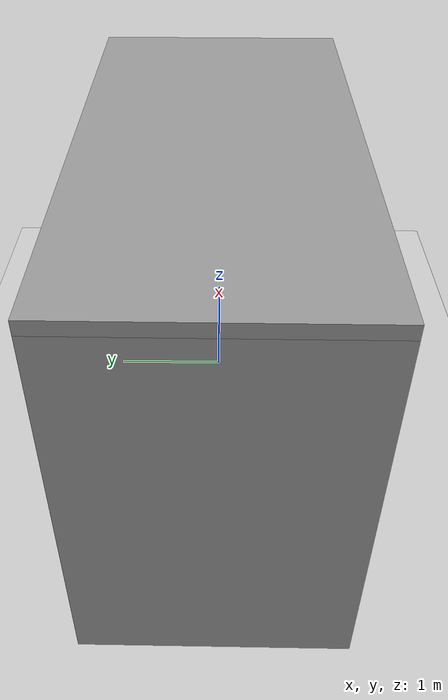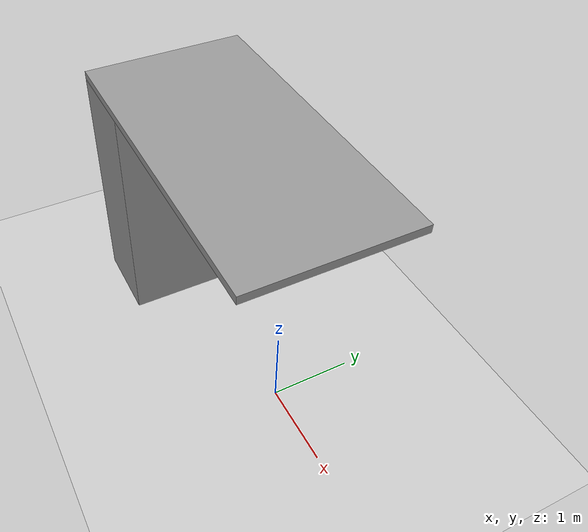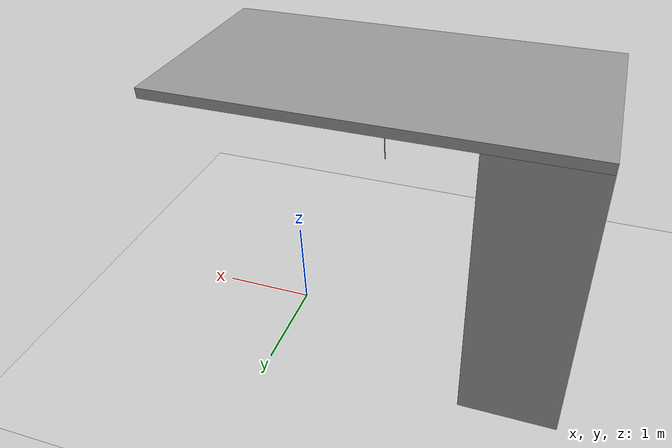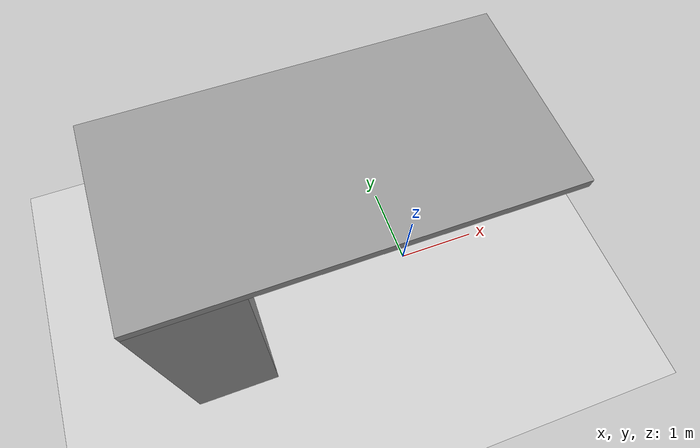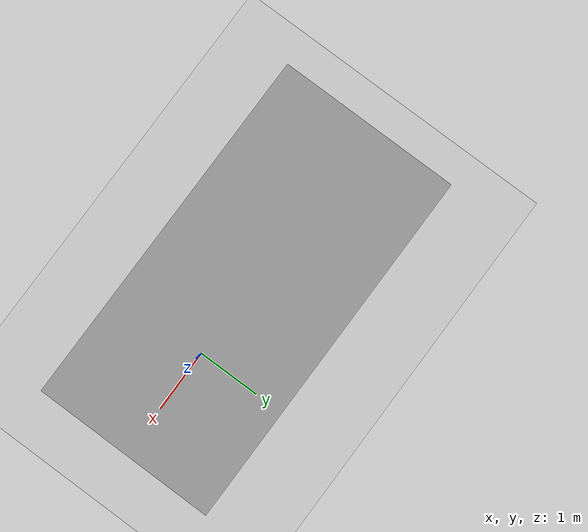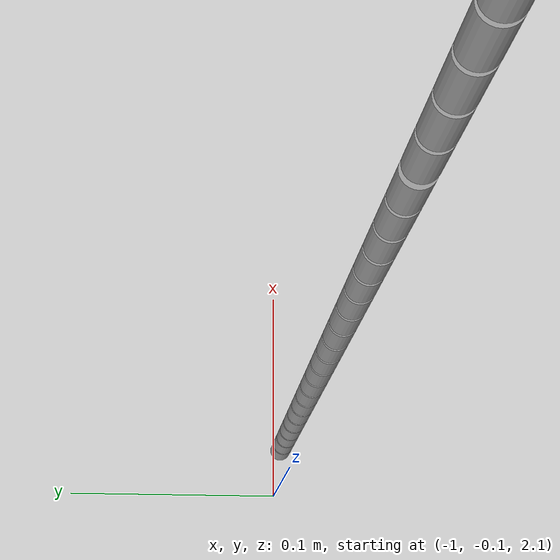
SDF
<sdf version="1.7">
 <world name="default">
  <light name="sun" type="directional">
   <pose>0 0 10 0 -0 0</pose>
   <diffuse>0.8 0.8 0.8 1</diffuse>
   <specular>0.2 0.2 0.2 1</specular>
   <attenuation>
    <range>1000</range>
    <constant>0.9</constant>
    <linear>0.01</linear>
    <quadratic>0.001</quadratic>
   </attenuation>
   <direction>-0.5 0.1 -0.9</direction>
   <spot><inner_angle>0</inner_angle><outer_angle>0</outer_angle><falloff>0</falloff></spot>
  </light>
  <model name="ground_plane">
   <static>1</static>
   <link name="link">
    <collision name="collision">
     <geometry><plane><normal>0 0 1</normal><size>100 100</size></plane></geometry>
     <surface>
      <contact><collide_bitmask>65535</collide_bitmask></contact>
      <friction><ode><mu>100</mu><mu2>50</mu2></ode></friction>
     </surface>
    </collision>
    <visual name="visual">
     <cast_shadows>0</cast_shadows>
     <geometry><plane><normal>0 0 1</normal><size>100 100</size></plane></geometry>
     <material>
      <script><uri>file://media/materials/scripts/gazebo.material</uri><name>Gazebo/Grey</name></script>
     </material>
    </visual>
   </link>
  </model>
  <gravity>0 0 -9.8</gravity>
  <magnetic_field>6e-06 2.3e-05 -4.2e-05</magnetic_field>
  <atmosphere type="adiabatic"/>
  <physics type="ode">
   <max_step_size>0.001</max_step_size>
   <real_time_factor>1</real_time_factor>
   <real_time_update_rate>1000</real_time_update_rate>
  </physics>
  <scene><ambient>0.4 0.4 0.4 1</ambient><background>0.7 0.7 0.7 1</background><shadows>1</shadows></scene>
  <spherical_coordinates>
   <surface_model>EARTH_WGS84</surface_model>
   <latitude_deg>0</latitude_deg>
   <longitude_deg>0</longitude_deg>
   <elevation>0</elevation>
   <heading_deg>0</heading_deg>
  </spherical_coordinates>
  <model name="hang_model">
   <link name="link">
    <inertial>
     <mass>220</mass>
     <inertia><ixx>238.333</ixx><ixy>0</ixy><ixz>0</ixz><iyy>183.333</iyy><iyz>0</iyz><izz>91.6667</izz></inertia>
     <pose>0 0 0 0 -0.03 0</pose>
    </inertial>
    <visual name="visual">
     <geometry><box><size>1 2 3</size></box></geometry>
     <material>
      <script><name>Gazebo/Grey</name><uri>file://media/materials/scripts/gazebo.material</uri></script>
      <shader type="pixel"><normal_map>__default__</normal_map></shader>
      <ambient>0.3 0.3 0.3 1</ambient>
      <diffuse>0.7 0.7 0.7 1</diffuse>
      <specular>0.01 0.01 0.01 1</specular>
      <emissive>0 0 0 1</emissive>
     </material>
    </visual>
    <collision name="collision">
     <geometry><box><size>1 2 3</size></box></geometry>
     <surface>
      <friction>
       <ode><mu>1</mu><mu2>1</mu2><fdir1>0 0 0</fdir1><slip1>0</slip1><slip2>0</slip2></ode>
       <torsional>
        <coefficient>1</coefficient>
        <patch_radius>0</patch_radius>
        <surface_radius>0</surface_radius>
        <use_patch_radius>1</use_patch_radius>
        <ode><slip>0</slip></ode>
       </torsional>
      </friction>
      <bounce><restitution_coefficient>0</restitution_coefficient><threshold>1e+06</threshold></bounce>
      <contact>
       <collide_without_contact>0</collide_without_contact>
       <collide_without_contact_bitmask>1</collide_without_contact_bitmask>
       <collide_bitmask>1</collide_bitmask>
       <ode>
        <soft_cfm>0</soft_cfm>
        <soft_erp>0.2</soft_erp>
        <kp>1e+13</kp>
        <kd>1</kd>
        <max_vel>0.01</max_vel>
        <min_depth>0</min_depth>
       </ode>
       <bullet>
        <split_impulse>1</split_impulse>
        <split_impulse_penetration_threshold>-0.01</split_impulse_penetration_threshold>
        <soft_cfm>0</soft_cfm>
        <soft_erp>0.2</soft_erp>
        <kp>1e+13</kp>
        <kd>1</kd>
       </bullet>
      </contact>
     </surface>
    </collision>
   </link>
   <link name="link_clone">
    <inertial>
     <mass>10</mass>
     <inertia><ixx>3.34167</ixx><ixy>0</ixy><ixz>0</ixz><iyy>13.3417</iyy><iyz>0</iyz><izz>16.6667</izz></inertia>
    </inertial>
    <pose>1.5 -0 1.55 0 -0 -0.000177</pose>
    <visual name="visual">
     <geometry><box><size>4 2 0.1</size></box></geometry>
     <material>
      <script><name>Gazebo/Grey</name><uri>file://media/materials/scripts/gazebo.material</uri></script>
      <shader type="pixel"><normal_map>__default__</normal_map></shader>
      <ambient>0.3 0.3 0.3 1</ambient>
      <diffuse>0.7 0.7 0.7 1</diffuse>
      <specular>0.01 0.01 0.01 1</specular>
      <emissive>0 0 0 1</emissive>
     </material>
    </visual>
    <collision name="collision">
     <geometry><box><size>4 2 0.1</size></box></geometry>
     <surface>
      <friction>
       <ode><mu>1</mu><mu2>1</mu2><fdir1>0 0 0</fdir1><slip1>0</slip1><slip2>0</slip2></ode>
       <torsional>
        <coefficient>1</coefficient>
        <patch_radius>0</patch_radius>
        <surface_radius>0</surface_radius>
        <use_patch_radius>1</use_patch_radius>
        <ode><slip>0</slip></ode>
       </torsional>
      </friction>
      <bounce><restitution_coefficient>0</restitution_coefficient><threshold>1e+06</threshold></bounce>
      <contact>
       <collide_without_contact>0</collide_without_contact>
       <collide_without_contact_bitmask>1</collide_without_contact_bitmask>
       <collide_bitmask>1</collide_bitmask>
       <ode>
        <soft_cfm>0</soft_cfm>
        <soft_erp>0.2</soft_erp>
        <kp>1e+13</kp>
        <kd>1</kd>
        <max_vel>0.01</max_vel>
        <min_depth>0</min_depth>
       </ode>
       <bullet>
        <split_impulse>1</split_impulse>
        <split_impulse_penetration_threshold>-0.01</split_impulse_penetration_threshold>
        <soft_cfm>0</soft_cfm>
        <soft_erp>0.2</soft_erp>
        <kp>1e+13</kp>
        <kd>1</kd>
       </bullet>
      </contact>
     </surface>
    </collision>
   </link>
   <joint name="link_JOINT_0" type="fixed">
    <parent>link</parent>
    <child>link_clone</child>
    <pose>-1.5 0 0 0 -0 0</pose>
    <physics>
     <ode><limit><cfm>0</cfm><erp>0.2</erp></limit><suspension><cfm>0</cfm><erp>0.2</erp></suspension></ode>
    </physics>
   </joint>
   <static>0</static>
   <pose>-2.59383 0.017354 1.5 -1e-06 -0 -0.00122</pose>
  </model>
  <model name="tether_test3">
   <link name="link_1">
    <inertial>
     <mass>0.005</mass>
     <inertia><ixx>7e-08</ixx><ixy>0</ixy><ixz>0</ixz><iyy>7e-08</iyy><iyz>0</iyz><izz>6e-08</izz></inertia>
    </inertial>
    <self_collide>1</self_collide>
    <visual name="visual">
     <geometry><cylinder><radius>0.005</radius><length>0.02</length></cylinder></geometry>
     <material>
      <lighting>1</lighting>
      <script><uri>file://media/materials/scripts/gazebo.material</uri><name>Gazebo/Grey</name></script>
      <shader type="pixel"><normal_map>__default__</normal_map></shader>
      <ambient>0.3 0.3 0.3 1</ambient>
      <diffuse>0.7 0.7 0.7 1</diffuse>
      <specular>0.01 0.01 0.01 1</specular>
      <emissive>0 0 0 1</emissive>
     </material>
    </visual>
    <collision name="collision">
     <geometry><cylinder><radius>0.005</radius><length>0.01</length></cylinder></geometry>
     <surface>
      <friction>
       <ode><mu>1</mu><mu2>1</mu2><fdir1>0 0 0</fdir1><slip1>0</slip1><slip2>0</slip2></ode>
       <torsional>
        <coefficient>1</coefficient>
        <patch_radius>0</patch_radius>
        <surface_radius>0</surface_radius>
        <use_patch_radius>1</use_patch_radius>
        <ode><slip>0</slip></ode>
       </torsional>
      </friction>
      <bounce><restitution_coefficient>0</restitution_coefficient><threshold>1e+06</threshold></bounce>
      <contact>
       <collide_without_contact>0</collide_without_contact>
       <collide_without_contact_bitmask>1</collide_without_contact_bitmask>
       <collide_bitmask>1</collide_bitmask>
       <ode>
        <soft_cfm>0</soft_cfm>
        <soft_erp>0.2</soft_erp>
        <kp>1e+13</kp>
        <kd>1</kd>
        <max_vel>0.01</max_vel>
        <min_depth>0</min_depth>
       </ode>
       <bullet>
        <split_impulse>1</split_impulse>
        <split_impulse_penetration_threshold>-0.01</split_impulse_penetration_threshold>
        <soft_cfm>0</soft_cfm>
        <soft_erp>0.2</soft_erp>
        <kp>1e+13</kp>
        <kd>1</kd>
       </bullet>
      </contact>
     </surface>
    </collision>
   </link>
   <link name="link_0_clone_clone_7">
    <inertial>
     <mass>0.005</mass>
     <inertia><ixx>7e-08</ixx><ixy>0</ixy><ixz>0</ixz><iyy>7e-08</iyy><iyz>0</iyz><izz>6e-08</izz></inertia>
    </inertial>
    <pose>0 0 0.264 0 -0 0</pose>
    <self_collide>1</self_collide>
    <visual name="visual">
     <geometry><cylinder><radius>0.005</radius><length>0.02</length></cylinder></geometry>
     <material>
      <lighting>1</lighting>
      <script><uri>file://media/materials/scripts/gazebo.material</uri><name>Gazebo/Grey</name></script>
      <shader type="pixel"><normal_map>__default__</normal_map></shader>
      <ambient>0.3 0.3 0.3 1</ambient>
      <diffuse>0.7 0.7 0.7 1</diffuse>
      <specular>0.01 0.01 0.01 1</specular>
      <emissive>0 0 0 1</emissive>
     </material>
    </visual>
    <collision name="collision">
     <geometry><cylinder><radius>0.005</radius><length>0.01</length></cylinder></geometry>
     <surface>
      <friction>
       <ode><mu>1</mu><mu2>1</mu2><fdir1>0 0 0</fdir1><slip1>0</slip1><slip2>0</slip2></ode>
       <torsional>
        <coefficient>1</coefficient>
        <patch_radius>0</patch_radius>
        <surface_radius>0</surface_radius>
        <use_patch_radius>1</use_patch_radius>
        <ode><slip>0</slip></ode>
       </torsional>
      </friction>
      <bounce><restitution_coefficient>0</restitution_coefficient><threshold>1e+06</threshold></bounce>
      <contact>
       <collide_without_contact>0</collide_without_contact>
       <collide_without_contact_bitmask>1</collide_without_contact_bitmask>
       <collide_bitmask>1</collide_bitmask>
       <ode>
        <soft_cfm>0</soft_cfm>
        <soft_erp>0.2</soft_erp>
        <kp>1e+13</kp>
        <kd>1</kd>
        <max_vel>0.01</max_vel>
        <min_depth>0</min_depth>
       </ode>
       <bullet>
        <split_impulse>1</split_impulse>
        <split_impulse_penetration_threshold>-0.01</split_impulse_penetration_threshold>
        <soft_cfm>0</soft_cfm>
        <soft_erp>0.2</soft_erp>
        <kp>1e+13</kp>
        <kd>1</kd>
       </bullet>
      </contact>
     </surface>
    </collision>
   </link>
   <link name="link_10">
    <inertial>
     <mass>0.005</mass>
     <inertia><ixx>7e-08</ixx><ixy>0</ixy><ixz>0</ixz><iyy>7e-08</iyy><iyz>0</iyz><izz>6e-08</izz></inertia>
    </inertial>
    <pose>0 0 0.154 0 -0 0</pose>
    <self_collide>1</self_collide>
    <visual name="visual">
     <geometry><cylinder><radius>0.005</radius><length>0.02</length></cylinder></geometry>
     <material>
      <lighting>1</lighting>
      <script><uri>file://media/materials/scripts/gazebo.material</uri><name>Gazebo/Grey</name></script>
      <shader type="pixel"><normal_map>__default__</normal_map></shader>
      <ambient>0.3 0.3 0.3 1</ambient>
      <diffuse>0.7 0.7 0.7 1</diffuse>
      <specular>0.01 0.01 0.01 1</specular>
      <emissive>0 0 0 1</emissive>
     </material>
    </visual>
    <collision name="collision">
     <geometry><cylinder><radius>0.005</radius><length>0.01</length></cylinder></geometry>
     <surface>
      <friction>
       <ode><mu>1</mu><mu2>1</mu2><fdir1>0 0 0</fdir1><slip1>0</slip1><slip2>0</slip2></ode>
       <torsional>
        <coefficient>1</coefficient>
        <patch_radius>0</patch_radius>
        <surface_radius>0</surface_radius>
        <use_patch_radius>1</use_patch_radius>
        <ode><slip>0</slip></ode>
       </torsional>
      </friction>
      <bounce><restitution_coefficient>0</restitution_coefficient><threshold>1e+06</threshold></bounce>
      <contact>
       <collide_without_contact>0</collide_without_contact>
       <collide_without_contact_bitmask>1</collide_without_contact_bitmask>
       <collide_bitmask>1</collide_bitmask>
       <ode>
        <soft_cfm>0</soft_cfm>
        <soft_erp>0.2</soft_erp>
        <kp>1e+13</kp>
        <kd>1</kd>
        <max_vel>0.01</max_vel>
        <min_depth>0</min_depth>
       </ode>
       <bullet>
        <split_impulse>1</split_impulse>
        <split_impulse_penetration_threshold>-0.01</split_impulse_penetration_threshold>
        <soft_cfm>0</soft_cfm>
        <soft_erp>0.2</soft_erp>
        <kp>1e+13</kp>
        <kd>1</kd>
       </bullet>
      </contact>
     </surface>
    </collision>
   </link>
   <link name="link_11">
    <inertial>
     <mass>0.005</mass>
     <inertia><ixx>7e-08</ixx><ixy>0</ixy><ixz>0</ixz><iyy>7e-08</iyy><iyz>0</iyz><izz>6e-08</izz></inertia>
    </inertial>
    <pose>0 0 0.132 0 -0 0</pose>
    <self_collide>1</self_collide>
    <visual name="visual">
     <geometry><cylinder><radius>0.005</radius><length>0.02</length></cylinder></geometry>
     <material>
      <lighting>1</lighting>
      <script><uri>file://media/materials/scripts/gazebo.material</uri><name>Gazebo/Grey</name></script>
      <shader type="pixel"><normal_map>__default__</normal_map></shader>
      <ambient>0.3 0.3 0.3 1</ambient>
      <diffuse>0.7 0.7 0.7 1</diffuse>
      <specular>0.01 0.01 0.01 1</specular>
      <emissive>0 0 0 1</emissive>
     </material>
    </visual>
    <collision name="collision">
     <geometry><cylinder><radius>0.005</radius><length>0.01</length></cylinder></geometry>
     <surface>
      <friction>
       <ode><mu>1</mu><mu2>1</mu2><fdir1>0 0 0</fdir1><slip1>0</slip1><slip2>0</slip2></ode>
       <torsional>
        <coefficient>1</coefficient>
        <patch_radius>0</patch_radius>
        <surface_radius>0</surface_radius>
        <use_patch_radius>1</use_patch_radius>
        <ode><slip>0</slip></ode>
       </torsional>
      </friction>
      <bounce><restitution_coefficient>0</restitution_coefficient><threshold>1e+06</threshold></bounce>
      <contact>
       <collide_without_contact>0</collide_without_contact>
       <collide_without_contact_bitmask>1</collide_without_contact_bitmask>
       <collide_bitmask>1</collide_bitmask>
       <ode>
        <soft_cfm>0</soft_cfm>
        <soft_erp>0.2</soft_erp>
        <kp>1e+13</kp>
        <kd>1</kd>
        <max_vel>0.01</max_vel>
        <min_depth>0</min_depth>
       </ode>
       <bullet>
        <split_impulse>1</split_impulse>
        <split_impulse_penetration_threshold>-0.01</split_impulse_penetration_threshold>
        <soft_cfm>0</soft_cfm>
        <soft_erp>0.2</soft_erp>
        <kp>1e+13</kp>
        <kd>1</kd>
       </bullet>
      </contact>
     </surface>
    </collision>
   </link>
   <link name="link_12">
    <inertial>
     <mass>0.005</mass>
     <inertia><ixx>7e-08</ixx><ixy>0</ixy><ixz>0</ixz><iyy>7e-08</iyy><iyz>0</iyz><izz>6e-08</izz></inertia>
    </inertial>
    <pose>0 0 0.286 0 -0 0</pose>
    <self_collide>1</self_collide>
    <visual name="visual">
     <geometry><cylinder><radius>0.005</radius><length>0.02</length></cylinder></geometry>
     <material>
      <lighting>1</lighting>
      <script><uri>file://media/materials/scripts/gazebo.material</uri><name>Gazebo/Grey</name></script>
      <shader type="pixel"><normal_map>__default__</normal_map></shader>
      <ambient>0.3 0.3 0.3 1</ambient>
      <diffuse>0.7 0.7 0.7 1</diffuse>
      <specular>0.01 0.01 0.01 1</specular>
      <emissive>0 0 0 1</emissive>
     </material>
    </visual>
    <collision name="collision">
     <geometry><cylinder><radius>0.005</radius><length>0.01</length></cylinder></geometry>
     <surface>
      <friction>
       <ode><mu>1</mu><mu2>1</mu2><fdir1>0 0 0</fdir1><slip1>0</slip1><slip2>0</slip2></ode>
       <torsional>
        <coefficient>1</coefficient>
        <patch_radius>0</patch_radius>
        <surface_radius>0</surface_radius>
        <use_patch_radius>1</use_patch_radius>
        <ode><slip>0</slip></ode>
       </torsional>
      </friction>
      <bounce><restitution_coefficient>0</restitution_coefficient><threshold>1e+06</threshold></bounce>
      <contact>
       <collide_without_contact>0</collide_without_contact>
       <collide_without_contact_bitmask>1</collide_without_contact_bitmask>
       <collide_bitmask>1</collide_bitmask>
       <ode>
        <soft_cfm>0</soft_cfm>
        <soft_erp>0.2</soft_erp>
        <kp>1e+13</kp>
        <kd>1</kd>
        <max_vel>0.01</max_vel>
        <min_depth>0</min_depth>
       </ode>
       <bullet>
        <split_impulse>1</split_impulse>
        <split_impulse_penetration_threshold>-0.01</split_impulse_penetration_threshold>
        <soft_cfm>0</soft_cfm>
        <soft_erp>0.2</soft_erp>
        <kp>1e+13</kp>
        <kd>1</kd>
       </bullet>
      </contact>
     </surface>
    </collision>
   </link>
   <link name="link_13">
    <inertial>
     <mass>0.005</mass>
     <inertia><ixx>7e-08</ixx><ixy>0</ixy><ixz>0</ixz><iyy>7e-08</iyy><iyz>0</iyz><izz>6e-08</izz></inertia>
    </inertial>
    <pose>0 0 0.308 0 -0 0</pose>
    <self_collide>1</self_collide>
    <visual name="visual">
     <geometry><cylinder><radius>0.005</radius><length>0.02</length></cylinder></geometry>
     <material>
      <lighting>1</lighting>
      <script><uri>file://media/materials/scripts/gazebo.material</uri><name>Gazebo/Grey</name></script>
      <shader type="pixel"><normal_map>__default__</normal_map></shader>
      <ambient>0.3 0.3 0.3 1</ambient>
      <diffuse>0.7 0.7 0.7 1</diffuse>
      <specular>0.01 0.01 0.01 1</specular>
      <emissive>0 0 0 1</emissive>
     </material>
    </visual>
    <collision name="collision">
     <geometry><cylinder><radius>0.005</radius><length>0.01</length></cylinder></geometry>
     <surface>
      <friction>
       <ode><mu>1</mu><mu2>1</mu2><fdir1>0 0 0</fdir1><slip1>0</slip1><slip2>0</slip2></ode>
       <torsional>
        <coefficient>1</coefficient>
        <patch_radius>0</patch_radius>
        <surface_radius>0</surface_radius>
        <use_patch_radius>1</use_patch_radius>
        <ode><slip>0</slip></ode>
       </torsional>
      </friction>
      <bounce><restitution_coefficient>0</restitution_coefficient><threshold>1e+06</threshold></bounce>
      <contact>
       <collide_without_contact>0</collide_without_contact>
       <collide_without_contact_bitmask>1</collide_without_contact_bitmask>
       <collide_bitmask>1</collide_bitmask>
       <ode>
        <soft_cfm>0</soft_cfm>
        <soft_erp>0.2</soft_erp>
        <kp>1e+13</kp>
        <kd>1</kd>
        <max_vel>0.01</max_vel>
        <min_depth>0</min_depth>
       </ode>
       <bullet>
        <split_impulse>1</split_impulse>
        <split_impulse_penetration_threshold>-0.01</split_impulse_penetration_threshold>
        <soft_cfm>0</soft_cfm>
        <soft_erp>0.2</soft_erp>
        <kp>1e+13</kp>
        <kd>1</kd>
       </bullet>
      </contact>
     </surface>
    </collision>
   </link>
   <link name="link_14">
    <inertial>
     <mass>0.005</mass>
     <inertia><ixx>7e-08</ixx><ixy>0</ixy><ixz>0</ixz><iyy>7e-08</iyy><iyz>0</iyz><izz>6e-08</izz></inertia>
    </inertial>
    <pose>0 0 0.33 0 -0 0</pose>
    <self_collide>1</self_collide>
    <visual name="visual">
     <geometry><cylinder><radius>0.005</radius><length>0.02</length></cylinder></geometry>
     <material>
      <lighting>1</lighting>
      <script><uri>file://media/materials/scripts/gazebo.material</uri><name>Gazebo/Grey</name></script>
      <shader type="pixel"><normal_map>__default__</normal_map></shader>
      <ambient>0.3 0.3 0.3 1</ambient>
      <diffuse>0.7 0.7 0.7 1</diffuse>
      <specular>0.01 0.01 0.01 1</specular>
      <emissive>0 0 0 1</emissive>
     </material>
    </visual>
    <collision name="collision">
     <geometry><cylinder><radius>0.005</radius><length>0.01</length></cylinder></geometry>
     <surface>
      <friction>
       <ode><mu>1</mu><mu2>1</mu2><fdir1>0 0 0</fdir1><slip1>0</slip1><slip2>0</slip2></ode>
       <torsional>
        <coefficient>1</coefficient>
        <patch_radius>0</patch_radius>
        <surface_radius>0</surface_radius>
        <use_patch_radius>1</use_patch_radius>
        <ode><slip>0</slip></ode>
       </torsional>
      </friction>
      <bounce><restitution_coefficient>0</restitution_coefficient><threshold>1e+06</threshold></bounce>
      <contact>
       <collide_without_contact>0</collide_without_contact>
       <collide_without_contact_bitmask>1</collide_without_contact_bitmask>
       <collide_bitmask>1</collide_bitmask>
       <ode>
        <soft_cfm>0</soft_cfm>
        <soft_erp>0.2</soft_erp>
        <kp>1e+13</kp>
        <kd>1</kd>
        <max_vel>0.01</max_vel>
        <min_depth>0</min_depth>
       </ode>
       <bullet>
        <split_impulse>1</split_impulse>
        <split_impulse_penetration_threshold>-0.01</split_impulse_penetration_threshold>
        <soft_cfm>0</soft_cfm>
        <soft_erp>0.2</soft_erp>
        <kp>1e+13</kp>
        <kd>1</kd>
       </bullet>
      </contact>
     </surface>
    </collision>
   </link>
   <link name="link_15">
    <inertial>
     <mass>0.005</mass>
     <inertia><ixx>7e-08</ixx><ixy>0</ixy><ixz>0</ixz><iyy>7e-08</iyy><iyz>0</iyz><izz>6e-08</izz></inertia>
    </inertial>
    <pose>0 0 0.352 0 -0 0</pose>
    <self_collide>1</self_collide>
    <visual name="visual">
     <geometry><cylinder><radius>0.005</radius><length>0.02</length></cylinder></geometry>
     <material>
      <lighting>1</lighting>
      <script><uri>file://media/materials/scripts/gazebo.material</uri><name>Gazebo/Grey</name></script>
      <shader type="pixel"><normal_map>__default__</normal_map></shader>
      <ambient>0.3 0.3 0.3 1</ambient>
      <diffuse>0.7 0.7 0.7 1</diffuse>
      <specular>0.01 0.01 0.01 1</specular>
      <emissive>0 0 0 1</emissive>
     </material>
    </visual>
    <collision name="collision">
     <geometry><cylinder><radius>0.005</radius><length>0.01</length></cylinder></geometry>
     <surface>
      <friction>
       <ode><mu>1</mu><mu2>1</mu2><fdir1>0 0 0</fdir1><slip1>0</slip1><slip2>0</slip2></ode>
       <torsional>
        <coefficient>1</coefficient>
        <patch_radius>0</patch_radius>
        <surface_radius>0</surface_radius>
        <use_patch_radius>1</use_patch_radius>
        <ode><slip>0</slip></ode>
       </torsional>
      </friction>
      <bounce><restitution_coefficient>0</restitution_coefficient><threshold>1e+06</threshold></bounce>
      <contact>
       <collide_without_contact>0</collide_without_contact>
       <collide_without_contact_bitmask>1</collide_without_contact_bitmask>
       <collide_bitmask>1</collide_bitmask>
       <ode>
        <soft_cfm>0</soft_cfm>
        <soft_erp>0.2</soft_erp>
        <kp>1e+13</kp>
        <kd>1</kd>
        <max_vel>0.01</max_vel>
        <min_depth>0</min_depth>
       </ode>
       <bullet>
        <split_impulse>1</split_impulse>
        <split_impulse_penetration_threshold>-0.01</split_impulse_penetration_threshold>
        <soft_cfm>0</soft_cfm>
        <soft_erp>0.2</soft_erp>
        <kp>1e+13</kp>
        <kd>1</kd>
       </bullet>
      </contact>
     </surface>
    </collision>
   </link>
   <link name="link_16">
    <inertial>
     <mass>0.005</mass>
     <inertia><ixx>7e-08</ixx><ixy>0</ixy><ixz>0</ixz><iyy>7e-08</iyy><iyz>0</iyz><izz>6e-08</izz></inertia>
    </inertial>
    <pose>0 0 0.374 0 -0 0</pose>
    <self_collide>1</self_collide>
    <visual name="visual">
     <geometry><cylinder><radius>0.005</radius><length>0.02</length></cylinder></geometry>
     <material>
      <lighting>1</lighting>
      <script><uri>file://media/materials/scripts/gazebo.material</uri><name>Gazebo/Grey</name></script>
      <shader type="pixel"><normal_map>__default__</normal_map></shader>
      <ambient>0.3 0.3 0.3 1</ambient>
      <diffuse>0.7 0.7 0.7 1</diffuse>
      <specular>0.01 0.01 0.01 1</specular>
      <emissive>0 0 0 1</emissive>
     </material>
    </visual>
    <collision name="collision">
     <geometry><cylinder><radius>0.005</radius><length>0.01</length></cylinder></geometry>
     <surface>
      <friction>
       <ode><mu>1</mu><mu2>1</mu2><fdir1>0 0 0</fdir1><slip1>0</slip1><slip2>0</slip2></ode>
       <torsional>
        <coefficient>1</coefficient>
        <patch_radius>0</patch_radius>
        <surface_radius>0</surface_radius>
        <use_patch_radius>1</use_patch_radius>
        <ode><slip>0</slip></ode>
       </torsional>
      </friction>
      <bounce><restitution_coefficient>0</restitution_coefficient><threshold>1e+06</threshold></bounce>
      <contact>
       <collide_without_contact>0</collide_without_contact>
       <collide_without_contact_bitmask>1</collide_without_contact_bitmask>
       <collide_bitmask>1</collide_bitmask>
       <ode>
        <soft_cfm>0</soft_cfm>
        <soft_erp>0.2</soft_erp>
        <kp>1e+13</kp>
        <kd>1</kd>
        <max_vel>0.01</max_vel>
        <min_depth>0</min_depth>
       </ode>
       <bullet>
        <split_impulse>1</split_impulse>
        <split_impulse_penetration_threshold>-0.01</split_impulse_penetration_threshold>
        <soft_cfm>0</soft_cfm>
        <soft_erp>0.2</soft_erp>
        <kp>1e+13</kp>
        <kd>1</kd>
       </bullet>
      </contact>
     </surface>
    </collision>
   </link>
   <link name="link_17">
    <inertial>
     <mass>0.005</mass>
     <inertia><ixx>7e-08</ixx><ixy>0</ixy><ixz>0</ixz><iyy>7e-08</iyy><iyz>0</iyz><izz>6e-08</izz></inertia>
    </inertial>
    <pose>0 0 0.552 0 -0 0</pose>
    <self_collide>1</self_collide>
    <visual name="visual">
     <geometry><cylinder><radius>0.005</radius><length>0.02</length></cylinder></geometry>
     <material>
      <lighting>1</lighting>
      <script><uri>file://media/materials/scripts/gazebo.material</uri><name>Gazebo/Grey</name></script>
      <shader type="pixel"><normal_map>__default__</normal_map></shader>
      <ambient>0.3 0.3 0.3 1</ambient>
      <diffuse>0.7 0.7 0.7 1</diffuse>
      <specular>0.01 0.01 0.01 1</specular>
      <emissive>0 0 0 1</emissive>
     </material>
    </visual>
    <collision name="collision">
     <geometry><cylinder><radius>0.005</radius><length>0.01</length></cylinder></geometry>
     <surface>
      <friction>
       <ode><mu>1</mu><mu2>1</mu2><fdir1>0 0 0</fdir1><slip1>0</slip1><slip2>0</slip2></ode>
       <torsional>
        <coefficient>1</coefficient>
        <patch_radius>0</patch_radius>
        <surface_radius>0</surface_radius>
        <use_patch_radius>1</use_patch_radius>
        <ode><slip>0</slip></ode>
       </torsional>
      </friction>
      <bounce><restitution_coefficient>0</restitution_coefficient><threshold>1e+06</threshold></bounce>
      <contact>
       <collide_without_contact>0</collide_without_contact>
       <collide_without_contact_bitmask>1</collide_without_contact_bitmask>
       <collide_bitmask>1</collide_bitmask>
       <ode>
        <soft_cfm>0</soft_cfm>
        <soft_erp>0.2</soft_erp>
        <kp>1e+13</kp>
        <kd>1</kd>
        <max_vel>0.01</max_vel>
        <min_depth>0</min_depth>
       </ode>
       <bullet>
        <split_impulse>1</split_impulse>
        <split_impulse_penetration_threshold>-0.01</split_impulse_penetration_threshold>
        <soft_cfm>0</soft_cfm>
        <soft_erp>0.2</soft_erp>
        <kp>1e+13</kp>
        <kd>1</kd>
       </bullet>
      </contact>
     </surface>
    </collision>
   </link>
   <link name="link_18">
    <inertial>
     <mass>0.005</mass>
     <inertia><ixx>7e-08</ixx><ixy>0</ixy><ixz>0</ixz><iyy>7e-08</iyy><iyz>0</iyz><izz>6e-08</izz></inertia>
    </inertial>
    <pose>0 0 0.574 0 -0 0</pose>
    <self_collide>1</self_collide>
    <visual name="visual">
     <geometry><cylinder><radius>0.005</radius><length>0.02</length></cylinder></geometry>
     <material>
      <lighting>1</lighting>
      <script><uri>file://media/materials/scripts/gazebo.material</uri><name>Gazebo/Grey</name></script>
      <shader type="pixel"><normal_map>__default__</normal_map></shader>
      <ambient>0.3 0.3 0.3 1</ambient>
      <diffuse>0.7 0.7 0.7 1</diffuse>
      <specular>0.01 0.01 0.01 1</specular>
      <emissive>0 0 0 1</emissive>
     </material>
    </visual>
    <collision name="collision">
     <geometry><cylinder><radius>0.005</radius><length>0.01</length></cylinder></geometry>
     <surface>
      <friction>
       <ode><mu>1</mu><mu2>1</mu2><fdir1>0 0 0</fdir1><slip1>0</slip1><slip2>0</slip2></ode>
       <torsional>
        <coefficient>1</coefficient>
        <patch_radius>0</patch_radius>
        <surface_radius>0</surface_radius>
        <use_patch_radius>1</use_patch_radius>
        <ode><slip>0</slip></ode>
       </torsional>
      </friction>
      <bounce><restitution_coefficient>0</restitution_coefficient><threshold>1e+06</threshold></bounce>
      <contact>
       <collide_without_contact>0</collide_without_contact>
       <collide_without_contact_bitmask>1</collide_without_contact_bitmask>
       <collide_bitmask>1</collide_bitmask>
       <ode>
        <soft_cfm>0</soft_cfm>
        <soft_erp>0.2</soft_erp>
        <kp>1e+13</kp>
        <kd>1</kd>
        <max_vel>0.01</max_vel>
        <min_depth>0</min_depth>
       </ode>
       <bullet>
        <split_impulse>1</split_impulse>
        <split_impulse_penetration_threshold>-0.01</split_impulse_penetration_threshold>
        <soft_cfm>0</soft_cfm>
        <soft_erp>0.2</soft_erp>
        <kp>1e+13</kp>
        <kd>1</kd>
       </bullet>
      </contact>
     </surface>
    </collision>
   </link>
   <link name="link_19">
    <inertial>
     <mass>0.005</mass>
     <inertia><ixx>7e-08</ixx><ixy>0</ixy><ixz>0</ixz><iyy>7e-08</iyy><iyz>0</iyz><izz>6e-08</izz></inertia>
    </inertial>
    <pose>0 0 0.596 0 -0 0</pose>
    <self_collide>1</self_collide>
    <visual name="visual">
     <geometry><cylinder><radius>0.005</radius><length>0.02</length></cylinder></geometry>
     <material>
      <lighting>1</lighting>
      <script><uri>file://media/materials/scripts/gazebo.material</uri><name>Gazebo/Grey</name></script>
      <shader type="pixel"><normal_map>__default__</normal_map></shader>
      <ambient>0.3 0.3 0.3 1</ambient>
      <diffuse>0.7 0.7 0.7 1</diffuse>
      <specular>0.01 0.01 0.01 1</specular>
      <emissive>0 0 0 1</emissive>
     </material>
    </visual>
    <collision name="collision">
     <geometry><cylinder><radius>0.005</radius><length>0.01</length></cylinder></geometry>
     <surface>
      <friction>
       <ode><mu>1</mu><mu2>1</mu2><fdir1>0 0 0</fdir1><slip1>0</slip1><slip2>0</slip2></ode>
       <torsional>
        <coefficient>1</coefficient>
        <patch_radius>0</patch_radius>
        <surface_radius>0</surface_radius>
        <use_patch_radius>1</use_patch_radius>
        <ode><slip>0</slip></ode>
       </torsional>
      </friction>
      <bounce><restitution_coefficient>0</restitution_coefficient><threshold>1e+06</threshold></bounce>
      <contact>
       <collide_without_contact>0</collide_without_contact>
       <collide_without_contact_bitmask>1</collide_without_contact_bitmask>
       <collide_bitmask>1</collide_bitmask>
       <ode>
        <soft_cfm>0</soft_cfm>
        <soft_erp>0.2</soft_erp>
        <kp>1e+13</kp>
        <kd>1</kd>
        <max_vel>0.01</max_vel>
        <min_depth>0</min_depth>
       </ode>
       <bullet>
        <split_impulse>1</split_impulse>
        <split_impulse_penetration_threshold>-0.01</split_impulse_penetration_threshold>
        <soft_cfm>0</soft_cfm>
        <soft_erp>0.2</soft_erp>
        <kp>1e+13</kp>
        <kd>1</kd>
       </bullet>
      </contact>
     </surface>
    </collision>
   </link>
   <link name="link_2">
    <inertial>
     <mass>0.005</mass>
     <inertia><ixx>7e-08</ixx><ixy>0</ixy><ixz>0</ixz><iyy>7e-08</iyy><iyz>0</iyz><izz>6e-08</izz></inertia>
    </inertial>
    <pose>0 0 0.11 0 -0 0</pose>
    <self_collide>1</self_collide>
    <visual name="visual">
     <geometry><cylinder><radius>0.005</radius><length>0.02</length></cylinder></geometry>
     <material>
      <lighting>1</lighting>
      <script><uri>file://media/materials/scripts/gazebo.material</uri><name>Gazebo/Grey</name></script>
      <shader type="pixel"><normal_map>__default__</normal_map></shader>
      <ambient>0.3 0.3 0.3 1</ambient>
      <diffuse>0.7 0.7 0.7 1</diffuse>
      <specular>0.01 0.01 0.01 1</specular>
      <emissive>0 0 0 1</emissive>
     </material>
    </visual>
    <collision name="collision">
     <geometry><cylinder><radius>0.005</radius><length>0.01</length></cylinder></geometry>
     <surface>
      <friction>
       <ode><mu>1</mu><mu2>1</mu2><fdir1>0 0 0</fdir1><slip1>0</slip1><slip2>0</slip2></ode>
       <torsional>
        <coefficient>1</coefficient>
        <patch_radius>0</patch_radius>
        <surface_radius>0</surface_radius>
        <use_patch_radius>1</use_patch_radius>
        <ode><slip>0</slip></ode>
       </torsional>
      </friction>
      <bounce><restitution_coefficient>0</restitution_coefficient><threshold>1e+06</threshold></bounce>
      <contact>
       <collide_without_contact>0</collide_without_contact>
       <collide_without_contact_bitmask>1</collide_without_contact_bitmask>
       <collide_bitmask>1</collide_bitmask>
       <ode>
        <soft_cfm>0</soft_cfm>
        <soft_erp>0.2</soft_erp>
        <kp>1e+13</kp>
        <kd>1</kd>
        <max_vel>0.01</max_vel>
        <min_depth>0</min_depth>
       </ode>
       <bullet>
        <split_impulse>1</split_impulse>
        <split_impulse_penetration_threshold>-0.01</split_impulse_penetration_threshold>
        <soft_cfm>0</soft_cfm>
        <soft_erp>0.2</soft_erp>
        <kp>1e+13</kp>
        <kd>1</kd>
       </bullet>
      </contact>
     </surface>
    </collision>
   </link>
   <link name="link_20">
    <inertial>
     <mass>0.005</mass>
     <inertia><ixx>7e-08</ixx><ixy>0</ixy><ixz>0</ixz><iyy>7e-08</iyy><iyz>0</iyz><izz>6e-08</izz></inertia>
    </inertial>
    <pose>0 0 0.618 0 -0 0</pose>
    <self_collide>1</self_collide>
    <visual name="visual">
     <geometry><cylinder><radius>0.005</radius><length>0.02</length></cylinder></geometry>
     <material>
      <lighting>1</lighting>
      <script><uri>file://media/materials/scripts/gazebo.material</uri><name>Gazebo/Grey</name></script>
      <shader type="pixel"><normal_map>__default__</normal_map></shader>
      <ambient>0.3 0.3 0.3 1</ambient>
      <diffuse>0.7 0.7 0.7 1</diffuse>
      <specular>0.01 0.01 0.01 1</specular>
      <emissive>0 0 0 1</emissive>
     </material>
    </visual>
    <collision name="collision">
     <geometry><cylinder><radius>0.005</radius><length>0.01</length></cylinder></geometry>
     <surface>
      <friction>
       <ode><mu>1</mu><mu2>1</mu2><fdir1>0 0 0</fdir1><slip1>0</slip1><slip2>0</slip2></ode>
       <torsional>
        <coefficient>1</coefficient>
        <patch_radius>0</patch_radius>
        <surface_radius>0</surface_radius>
        <use_patch_radius>1</use_patch_radius>
        <ode><slip>0</slip></ode>
       </torsional>
      </friction>
      <bounce><restitution_coefficient>0</restitution_coefficient><threshold>1e+06</threshold></bounce>
      <contact>
       <collide_without_contact>0</collide_without_contact>
       <collide_without_contact_bitmask>1</collide_without_contact_bitmask>
       <collide_bitmask>1</collide_bitmask>
       <ode>
        <soft_cfm>0</soft_cfm>
        <soft_erp>0.2</soft_erp>
        <kp>1e+13</kp>
        <kd>1</kd>
        <max_vel>0.01</max_vel>
        <min_depth>0</min_depth>
       </ode>
       <bullet>
        <split_impulse>1</split_impulse>
        <split_impulse_penetration_threshold>-0.01</split_impulse_penetration_threshold>
        <soft_cfm>0</soft_cfm>
        <soft_erp>0.2</soft_erp>
        <kp>1e+13</kp>
        <kd>1</kd>
       </bullet>
      </contact>
     </surface>
    </collision>
   </link>
   <link name="link_21">
    <inertial>
     <mass>0.005</mass>
     <inertia><ixx>7e-08</ixx><ixy>0</ixy><ixz>0</ixz><iyy>7e-08</iyy><iyz>0</iyz><izz>6e-08</izz></inertia>
    </inertial>
    <pose>0 0 0.64 0 -0 0</pose>
    <self_collide>1</self_collide>
    <visual name="visual">
     <geometry><cylinder><radius>0.005</radius><length>0.02</length></cylinder></geometry>
     <material>
      <lighting>1</lighting>
      <script><uri>file://media/materials/scripts/gazebo.material</uri><name>Gazebo/Grey</name></script>
      <shader type="pixel"><normal_map>__default__</normal_map></shader>
      <ambient>0.3 0.3 0.3 1</ambient>
      <diffuse>0.7 0.7 0.7 1</diffuse>
      <specular>0.01 0.01 0.01 1</specular>
      <emissive>0 0 0 1</emissive>
     </material>
    </visual>
    <collision name="collision">
     <geometry><cylinder><radius>0.005</radius><length>0.01</length></cylinder></geometry>
     <surface>
      <friction>
       <ode><mu>1</mu><mu2>1</mu2><fdir1>0 0 0</fdir1><slip1>0</slip1><slip2>0</slip2></ode>
       <torsional>
        <coefficient>1</coefficient>
        <patch_radius>0</patch_radius>
        <surface_radius>0</surface_radius>
        <use_patch_radius>1</use_patch_radius>
        <ode><slip>0</slip></ode>
       </torsional>
      </friction>
      <bounce><restitution_coefficient>0</restitution_coefficient><threshold>1e+06</threshold></bounce>
      <contact>
       <collide_without_contact>0</collide_without_contact>
       <collide_without_contact_bitmask>1</collide_without_contact_bitmask>
       <collide_bitmask>1</collide_bitmask>
       <ode>
        <soft_cfm>0</soft_cfm>
        <soft_erp>0.2</soft_erp>
        <kp>1e+13</kp>
        <kd>1</kd>
        <max_vel>0.01</max_vel>
        <min_depth>0</min_depth>
       </ode>
       <bullet>
        <split_impulse>1</split_impulse>
        <split_impulse_penetration_threshold>-0.01</split_impulse_penetration_threshold>
        <soft_cfm>0</soft_cfm>
        <soft_erp>0.2</soft_erp>
        <kp>1e+13</kp>
        <kd>1</kd>
       </bullet>
      </contact>
     </surface>
    </collision>
   </link>
   <link name="link_22">
    <inertial>
     <mass>0.005</mass>
     <inertia><ixx>7e-08</ixx><ixy>0</ixy><ixz>0</ixz><iyy>7e-08</iyy><iyz>0</iyz><izz>6e-08</izz></inertia>
    </inertial>
    <pose>0 0 0.662 0 -0 0</pose>
    <self_collide>1</self_collide>
    <visual name="visual">
     <geometry><cylinder><radius>0.005</radius><length>0.02</length></cylinder></geometry>
     <material>
      <lighting>1</lighting>
      <script><uri>file://media/materials/scripts/gazebo.material</uri><name>Gazebo/Grey</name></script>
      <shader type="pixel"><normal_map>__default__</normal_map></shader>
      <ambient>0.3 0.3 0.3 1</ambient>
      <diffuse>0.7 0.7 0.7 1</diffuse>
      <specular>0.01 0.01 0.01 1</specular>
      <emissive>0 0 0 1</emissive>
     </material>
    </visual>
    <collision name="collision">
     <geometry><cylinder><radius>0.005</radius><length>0.01</length></cylinder></geometry>
     <surface>
      <friction>
       <ode><mu>1</mu><mu2>1</mu2><fdir1>0 0 0</fdir1><slip1>0</slip1><slip2>0</slip2></ode>
       <torsional>
        <coefficient>1</coefficient>
        <patch_radius>0</patch_radius>
        <surface_radius>0</surface_radius>
        <use_patch_radius>1</use_patch_radius>
        <ode><slip>0</slip></ode>
       </torsional>
      </friction>
      <bounce><restitution_coefficient>0</restitution_coefficient><threshold>1e+06</threshold></bounce>
      <contact>
       <collide_without_contact>0</collide_without_contact>
       <collide_without_contact_bitmask>1</collide_without_contact_bitmask>
       <collide_bitmask>1</collide_bitmask>
       <ode>
        <soft_cfm>0</soft_cfm>
        <soft_erp>0.2</soft_erp>
        <kp>1e+13</kp>
        <kd>1</kd>
        <max_vel>0.01</max_vel>
        <min_depth>0</min_depth>
       </ode>
       <bullet>
        <split_impulse>1</split_impulse>
        <split_impulse_penetration_threshold>-0.01</split_impulse_penetration_threshold>
        <soft_cfm>0</soft_cfm>
        <soft_erp>0.2</soft_erp>
        <kp>1e+13</kp>
        <kd>1</kd>
       </bullet>
      </contact>
     </surface>
    </collision>
   </link>
   <link name="link_23">
    <inertial>
     <mass>0.005</mass>
     <inertia><ixx>7e-08</ixx><ixy>0</ixy><ixz>0</ixz><iyy>7e-08</iyy><iyz>0</iyz><izz>6e-08</izz></inertia>
    </inertial>
    <pose>0 0 0.684 0 -0 0</pose>
    <self_collide>1</self_collide>
    <visual name="visual">
     <geometry><cylinder><radius>0.005</radius><length>0.02</length></cylinder></geometry>
     <material>
      <lighting>1</lighting>
      <script><uri>file://media/materials/scripts/gazebo.material</uri><name>Gazebo/Grey</name></script>
      <shader type="pixel"><normal_map>__default__</normal_map></shader>
      <ambient>0.3 0.3 0.3 1</ambient>
      <diffuse>0.7 0.7 0.7 1</diffuse>
      <specular>0.01 0.01 0.01 1</specular>
      <emissive>0 0 0 1</emissive>
     </material>
    </visual>
    <collision name="collision">
     <geometry><cylinder><radius>0.005</radius><length>0.01</length></cylinder></geometry>
     <surface>
      <friction>
       <ode><mu>1</mu><mu2>1</mu2><fdir1>0 0 0</fdir1><slip1>0</slip1><slip2>0</slip2></ode>
       <torsional>
        <coefficient>1</coefficient>
        <patch_radius>0</patch_radius>
        <surface_radius>0</surface_radius>
        <use_patch_radius>1</use_patch_radius>
        <ode><slip>0</slip></ode>
       </torsional>
      </friction>
      <bounce><restitution_coefficient>0</restitution_coefficient><threshold>1e+06</threshold></bounce>
      <contact>
       <collide_without_contact>0</collide_without_contact>
       <collide_without_contact_bitmask>1</collide_without_contact_bitmask>
       <collide_bitmask>1</collide_bitmask>
       <ode>
        <soft_cfm>0</soft_cfm>
        <soft_erp>0.2</soft_erp>
        <kp>1e+13</kp>
        <kd>1</kd>
        <max_vel>0.01</max_vel>
        <min_depth>0</min_depth>
       </ode>
       <bullet>
        <split_impulse>1</split_impulse>
        <split_impulse_penetration_threshold>-0.01</split_impulse_penetration_threshold>
        <soft_cfm>0</soft_cfm>
        <soft_erp>0.2</soft_erp>
        <kp>1e+13</kp>
        <kd>1</kd>
       </bullet>
      </contact>
     </surface>
    </collision>
   </link>
   <link name="link_24">
    <inertial>
     <mass>0.005</mass>
     <inertia><ixx>7e-08</ixx><ixy>0</ixy><ixz>0</ixz><iyy>7e-08</iyy><iyz>0</iyz><izz>6e-08</izz></inertia>
    </inertial>
    <pose>0 0 0.706 0 -0 0</pose>
    <self_collide>1</self_collide>
    <visual name="visual">
     <geometry><cylinder><radius>0.005</radius><length>0.02</length></cylinder></geometry>
     <material>
      <lighting>1</lighting>
      <script><uri>file://media/materials/scripts/gazebo.material</uri><name>Gazebo/Grey</name></script>
      <shader type="pixel"><normal_map>__default__</normal_map></shader>
      <ambient>0.3 0.3 0.3 1</ambient>
      <diffuse>0.7 0.7 0.7 1</diffuse>
      <specular>0.01 0.01 0.01 1</specular>
      <emissive>0 0 0 1</emissive>
     </material>
    </visual>
    <collision name="collision">
     <geometry><cylinder><radius>0.005</radius><length>0.01</length></cylinder></geometry>
     <surface>
      <friction>
       <ode><mu>1</mu><mu2>1</mu2><fdir1>0 0 0</fdir1><slip1>0</slip1><slip2>0</slip2></ode>
       <torsional>
        <coefficient>1</coefficient>
        <patch_radius>0</patch_radius>
        <surface_radius>0</surface_radius>
        <use_patch_radius>1</use_patch_radius>
        <ode><slip>0</slip></ode>
       </torsional>
      </friction>
      <bounce><restitution_coefficient>0</restitution_coefficient><threshold>1e+06</threshold></bounce>
      <contact>
       <collide_without_contact>0</collide_without_contact>
       <collide_without_contact_bitmask>1</collide_without_contact_bitmask>
       <collide_bitmask>1</collide_bitmask>
       <ode>
        <soft_cfm>0</soft_cfm>
        <soft_erp>0.2</soft_erp>
        <kp>1e+13</kp>
        <kd>1</kd>
        <max_vel>0.01</max_vel>
        <min_depth>0</min_depth>
       </ode>
       <bullet>
        <split_impulse>1</split_impulse>
        <split_impulse_penetration_threshold>-0.01</split_impulse_penetration_threshold>
        <soft_cfm>0</soft_cfm>
        <soft_erp>0.2</soft_erp>
        <kp>1e+13</kp>
        <kd>1</kd>
       </bullet>
      </contact>
     </surface>
    </collision>
   </link>
   <link name="link_25">
    <inertial>
     <mass>0.005</mass>
     <inertia><ixx>7e-08</ixx><ixy>0</ixy><ixz>0</ixz><iyy>7e-08</iyy><iyz>0</iyz><izz>6e-08</izz></inertia>
    </inertial>
    <pose>0 0 0.728 0 -0 0</pose>
    <self_collide>1</self_collide>
    <visual name="visual">
     <geometry><cylinder><radius>0.005</radius><length>0.02</length></cylinder></geometry>
     <material>
      <lighting>1</lighting>
      <script><uri>file://media/materials/scripts/gazebo.material</uri><name>Gazebo/Grey</name></script>
      <shader type="pixel"><normal_map>__default__</normal_map></shader>
      <ambient>0.3 0.3 0.3 1</ambient>
      <diffuse>0.7 0.7 0.7 1</diffuse>
      <specular>0.01 0.01 0.01 1</specular>
      <emissive>0 0 0 1</emissive>
     </material>
    </visual>
    <collision name="collision">
     <geometry><cylinder><radius>0.005</radius><length>0.01</length></cylinder></geometry>
     <surface>
      <friction>
       <ode><mu>1</mu><mu2>1</mu2><fdir1>0 0 0</fdir1><slip1>0</slip1><slip2>0</slip2></ode>
       <torsional>
        <coefficient>1</coefficient>
        <patch_radius>0</patch_radius>
        <surface_radius>0</surface_radius>
        <use_patch_radius>1</use_patch_radius>
        <ode><slip>0</slip></ode>
       </torsional>
      </friction>
      <bounce><restitution_coefficient>0</restitution_coefficient><threshold>1e+06</threshold></bounce>
      <contact>
       <collide_without_contact>0</collide_without_contact>
       <collide_without_contact_bitmask>1</collide_without_contact_bitmask>
       <collide_bitmask>1</collide_bitmask>
       <ode>
        <soft_cfm>0</soft_cfm>
        <soft_erp>0.2</soft_erp>
        <kp>1e+13</kp>
        <kd>1</kd>
        <max_vel>0.01</max_vel>
        <min_depth>0</min_depth>
       </ode>
       <bullet>
        <split_impulse>1</split_impulse>
        <split_impulse_penetration_threshold>-0.01</split_impulse_penetration_threshold>
        <soft_cfm>0</soft_cfm>
        <soft_erp>0.2</soft_erp>
        <kp>1e+13</kp>
        <kd>1</kd>
       </bullet>
      </contact>
     </surface>
    </collision>
   </link>
   <link name="link_26">
    <inertial>
     <mass>0.005</mass>
     <inertia><ixx>7e-08</ixx><ixy>0</ixy><ixz>0</ixz><iyy>7e-08</iyy><iyz>0</iyz><izz>6e-08</izz></inertia>
    </inertial>
    <pose>0 0 0.75 0 -0 0</pose>
    <self_collide>1</self_collide>
    <visual name="visual">
     <geometry><cylinder><radius>0.005</radius><length>0.02</length></cylinder></geometry>
     <material>
      <lighting>1</lighting>
      <script><uri>file://media/materials/scripts/gazebo.material</uri><name>Gazebo/Grey</name></script>
      <shader type="pixel"><normal_map>__default__</normal_map></shader>
      <ambient>0.3 0.3 0.3 1</ambient>
      <diffuse>0.7 0.7 0.7 1</diffuse>
      <specular>0.01 0.01 0.01 1</specular>
      <emissive>0 0 0 1</emissive>
     </material>
    </visual>
    <collision name="collision">
     <geometry><cylinder><radius>0.005</radius><length>0.01</length></cylinder></geometry>
     <surface>
      <friction>
       <ode><mu>1</mu><mu2>1</mu2><fdir1>0 0 0</fdir1><slip1>0</slip1><slip2>0</slip2></ode>
       <torsional>
        <coefficient>1</coefficient>
        <patch_radius>0</patch_radius>
        <surface_radius>0</surface_radius>
        <use_patch_radius>1</use_patch_radius>
        <ode><slip>0</slip></ode>
       </torsional>
      </friction>
      <bounce><restitution_coefficient>0</restitution_coefficient><threshold>1e+06</threshold></bounce>
      <contact>
       <collide_without_contact>0</collide_without_contact>
       <collide_without_contact_bitmask>1</collide_without_contact_bitmask>
       <collide_bitmask>1</collide_bitmask>
       <ode>
        <soft_cfm>0</soft_cfm>
        <soft_erp>0.2</soft_erp>
        <kp>1e+13</kp>
        <kd>1</kd>
        <max_vel>0.01</max_vel>
        <min_depth>0</min_depth>
       </ode>
       <bullet>
        <split_impulse>1</split_impulse>
        <split_impulse_penetration_threshold>-0.01</split_impulse_penetration_threshold>
        <soft_cfm>0</soft_cfm>
        <soft_erp>0.2</soft_erp>
        <kp>1e+13</kp>
        <kd>1</kd>
       </bullet>
      </contact>
     </surface>
    </collision>
   </link>
   <link name="link_27">
    <inertial>
     <mass>0.005</mass>
     <inertia><ixx>7e-08</ixx><ixy>0</ixy><ixz>0</ixz><iyy>7e-08</iyy><iyz>0</iyz><izz>6e-08</izz></inertia>
    </inertial>
    <pose>0 0 0.772 0 -0 0</pose>
    <self_collide>1</self_collide>
    <visual name="visual">
     <geometry><cylinder><radius>0.005</radius><length>0.02</length></cylinder></geometry>
     <material>
      <lighting>1</lighting>
      <script><uri>file://media/materials/scripts/gazebo.material</uri><name>Gazebo/Grey</name></script>
      <shader type="pixel"><normal_map>__default__</normal_map></shader>
      <ambient>0.3 0.3 0.3 1</ambient>
      <diffuse>0.7 0.7 0.7 1</diffuse>
      <specular>0.01 0.01 0.01 1</specular>
      <emissive>0 0 0 1</emissive>
     </material>
    </visual>
    <collision name="collision">
     <geometry><cylinder><radius>0.005</radius><length>0.01</length></cylinder></geometry>
     <surface>
      <friction>
       <ode><mu>1</mu><mu2>1</mu2><fdir1>0 0 0</fdir1><slip1>0</slip1><slip2>0</slip2></ode>
       <torsional>
        <coefficient>1</coefficient>
        <patch_radius>0</patch_radius>
        <surface_radius>0</surface_radius>
        <use_patch_radius>1</use_patch_radius>
        <ode><slip>0</slip></ode>
       </torsional>
      </friction>
      <bounce><restitution_coefficient>0</restitution_coefficient><threshold>1e+06</threshold></bounce>
      <contact>
       <collide_without_contact>0</collide_without_contact>
       <collide_without_contact_bitmask>1</collide_without_contact_bitmask>
       <collide_bitmask>1</collide_bitmask>
       <ode>
        <soft_cfm>0</soft_cfm>
        <soft_erp>0.2</soft_erp>
        <kp>1e+13</kp>
        <kd>1</kd>
        <max_vel>0.01</max_vel>
        <min_depth>0</min_depth>
       </ode>
       <bullet>
        <split_impulse>1</split_impulse>
        <split_impulse_penetration_threshold>-0.01</split_impulse_penetration_threshold>
        <soft_cfm>0</soft_cfm>
        <soft_erp>0.2</soft_erp>
        <kp>1e+13</kp>
        <kd>1</kd>
       </bullet>
      </contact>
     </surface>
    </collision>
   </link>
   <link name="link_28">
    <inertial>
     <mass>0.005</mass>
     <inertia><ixx>7e-08</ixx><ixy>0</ixy><ixz>0</ixz><iyy>7e-08</iyy><iyz>0</iyz><izz>6e-08</izz></inertia>
    </inertial>
    <pose>0 0 0.794 0 -0 0</pose>
    <self_collide>1</self_collide>
    <visual name="visual">
     <geometry><cylinder><radius>0.005</radius><length>0.02</length></cylinder></geometry>
     <material>
      <lighting>1</lighting>
      <script><uri>file://media/materials/scripts/gazebo.material</uri><name>Gazebo/Grey</name></script>
      <shader type="pixel"><normal_map>__default__</normal_map></shader>
      <ambient>0.3 0.3 0.3 1</ambient>
      <diffuse>0.7 0.7 0.7 1</diffuse>
      <specular>0.01 0.01 0.01 1</specular>
      <emissive>0 0 0 1</emissive>
     </material>
    </visual>
    <collision name="collision">
     <geometry><cylinder><radius>0.005</radius><length>0.01</length></cylinder></geometry>
     <surface>
      <friction>
       <ode><mu>1</mu><mu2>1</mu2><fdir1>0 0 0</fdir1><slip1>0</slip1><slip2>0</slip2></ode>
       <torsional>
        <coefficient>1</coefficient>
        <patch_radius>0</patch_radius>
        <surface_radius>0</surface_radius>
        <use_patch_radius>1</use_patch_radius>
        <ode><slip>0</slip></ode>
       </torsional>
      </friction>
      <bounce><restitution_coefficient>0</restitution_coefficient><threshold>1e+06</threshold></bounce>
      <contact>
       <collide_without_contact>0</collide_without_contact>
       <collide_without_contact_bitmask>1</collide_without_contact_bitmask>
       <collide_bitmask>1</collide_bitmask>
       <ode>
        <soft_cfm>0</soft_cfm>
        <soft_erp>0.2</soft_erp>
        <kp>1e+13</kp>
        <kd>1</kd>
        <max_vel>0.01</max_vel>
        <min_depth>0</min_depth>
       </ode>
       <bullet>
        <split_impulse>1</split_impulse>
        <split_impulse_penetration_threshold>-0.01</split_impulse_penetration_threshold>
        <soft_cfm>0</soft_cfm>
        <soft_erp>0.2</soft_erp>
        <kp>1e+13</kp>
        <kd>1</kd>
       </bullet>
      </contact>
     </surface>
    </collision>
   </link>
   <link name="link_29">
    <inertial>
     <mass>0.005</mass>
     <inertia><ixx>7e-08</ixx><ixy>0</ixy><ixz>0</ixz><iyy>7e-08</iyy><iyz>0</iyz><izz>6e-08</izz></inertia>
    </inertial>
    <pose>0 0 0.816 0 -0 0</pose>
    <self_collide>1</self_collide>
    <visual name="visual">
     <geometry><cylinder><radius>0.005</radius><length>0.02</length></cylinder></geometry>
     <material>
      <lighting>1</lighting>
      <script><uri>file://media/materials/scripts/gazebo.material</uri><name>Gazebo/Grey</name></script>
      <shader type="pixel"><normal_map>__default__</normal_map></shader>
      <ambient>0.3 0.3 0.3 1</ambient>
      <diffuse>0.7 0.7 0.7 1</diffuse>
      <specular>0.01 0.01 0.01 1</specular>
      <emissive>0 0 0 1</emissive>
     </material>
    </visual>
    <collision name="collision">
     <geometry><cylinder><radius>0.005</radius><length>0.01</length></cylinder></geometry>
     <surface>
      <friction>
       <ode><mu>1</mu><mu2>1</mu2><fdir1>0 0 0</fdir1><slip1>0</slip1><slip2>0</slip2></ode>
       <torsional>
        <coefficient>1</coefficient>
        <patch_radius>0</patch_radius>
        <surface_radius>0</surface_radius>
        <use_patch_radius>1</use_patch_radius>
        <ode><slip>0</slip></ode>
       </torsional>
      </friction>
      <bounce><restitution_coefficient>0</restitution_coefficient><threshold>1e+06</threshold></bounce>
      <contact>
       <collide_without_contact>0</collide_without_contact>
       <collide_without_contact_bitmask>1</collide_without_contact_bitmask>
       <collide_bitmask>1</collide_bitmask>
       <ode>
        <soft_cfm>0</soft_cfm>
        <soft_erp>0.2</soft_erp>
        <kp>1e+13</kp>
        <kd>1</kd>
        <max_vel>0.01</max_vel>
        <min_depth>0</min_depth>
       </ode>
       <bullet>
        <split_impulse>1</split_impulse>
        <split_impulse_penetration_threshold>-0.01</split_impulse_penetration_threshold>
        <soft_cfm>0</soft_cfm>
        <soft_erp>0.2</soft_erp>
        <kp>1e+13</kp>
        <kd>1</kd>
       </bullet>
      </contact>
     </surface>
    </collision>
   </link>
   <link name="link_3">
    <inertial>
     <mass>0.005</mass>
     <inertia><ixx>7e-08</ixx><ixy>0</ixy><ixz>0</ixz><iyy>7e-08</iyy><iyz>0</iyz><izz>6e-08</izz></inertia>
    </inertial>
    <pose>0 0 0.022 0 -0 0</pose>
    <self_collide>1</self_collide>
    <visual name="visual">
     <geometry><cylinder><radius>0.005</radius><length>0.02</length></cylinder></geometry>
     <material>
      <lighting>1</lighting>
      <script><uri>file://media/materials/scripts/gazebo.material</uri><name>Gazebo/Grey</name></script>
      <shader type="pixel"><normal_map>__default__</normal_map></shader>
      <ambient>0.3 0.3 0.3 1</ambient>
      <diffuse>0.7 0.7 0.7 1</diffuse>
      <specular>0.01 0.01 0.01 1</specular>
      <emissive>0 0 0 1</emissive>
     </material>
    </visual>
    <collision name="collision">
     <geometry><cylinder><radius>0.005</radius><length>0.01</length></cylinder></geometry>
     <surface>
      <friction>
       <ode><mu>1</mu><mu2>1</mu2><fdir1>0 0 0</fdir1><slip1>0</slip1><slip2>0</slip2></ode>
       <torsional>
        <coefficient>1</coefficient>
        <patch_radius>0</patch_radius>
        <surface_radius>0</surface_radius>
        <use_patch_radius>1</use_patch_radius>
        <ode><slip>0</slip></ode>
       </torsional>
      </friction>
      <bounce><restitution_coefficient>0</restitution_coefficient><threshold>1e+06</threshold></bounce>
      <contact>
       <collide_without_contact>0</collide_without_contact>
       <collide_without_contact_bitmask>1</collide_without_contact_bitmask>
       <collide_bitmask>1</collide_bitmask>
       <ode>
        <soft_cfm>0</soft_cfm>
        <soft_erp>0.2</soft_erp>
        <kp>1e+13</kp>
        <kd>1</kd>
        <max_vel>0.01</max_vel>
        <min_depth>0</min_depth>
       </ode>
       <bullet>
        <split_impulse>1</split_impulse>
        <split_impulse_penetration_threshold>-0.01</split_impulse_penetration_threshold>
        <soft_cfm>0</soft_cfm>
        <soft_erp>0.2</soft_erp>
        <kp>1e+13</kp>
        <kd>1</kd>
       </bullet>
      </contact>
     </surface>
    </collision>
   </link>
   <link name="link_30">
    <inertial>
     <mass>0.005</mass>
     <inertia><ixx>7e-08</ixx><ixy>0</ixy><ixz>0</ixz><iyy>7e-08</iyy><iyz>0</iyz><izz>6e-08</izz></inertia>
    </inertial>
    <pose>0 0 0.838 0 -0 0</pose>
    <self_collide>1</self_collide>
    <visual name="visual">
     <geometry><cylinder><radius>0.005</radius><length>0.02</length></cylinder></geometry>
     <material>
      <lighting>1</lighting>
      <script><uri>file://media/materials/scripts/gazebo.material</uri><name>Gazebo/Grey</name></script>
      <shader type="pixel"><normal_map>__default__</normal_map></shader>
      <ambient>0.3 0.3 0.3 1</ambient>
      <diffuse>0.7 0.7 0.7 1</diffuse>
      <specular>0.01 0.01 0.01 1</specular>
      <emissive>0 0 0 1</emissive>
     </material>
    </visual>
    <collision name="collision">
     <geometry><cylinder><radius>0.005</radius><length>0.01</length></cylinder></geometry>
     <surface>
      <friction>
       <ode><mu>1</mu><mu2>1</mu2><fdir1>0 0 0</fdir1><slip1>0</slip1><slip2>0</slip2></ode>
       <torsional>
        <coefficient>1</coefficient>
        <patch_radius>0</patch_radius>
        <surface_radius>0</surface_radius>
        <use_patch_radius>1</use_patch_radius>
        <ode><slip>0</slip></ode>
       </torsional>
      </friction>
      <bounce><restitution_coefficient>0</restitution_coefficient><threshold>1e+06</threshold></bounce>
      <contact>
       <collide_without_contact>0</collide_without_contact>
       <collide_without_contact_bitmask>1</collide_without_contact_bitmask>
       <collide_bitmask>1</collide_bitmask>
       <ode>
        <soft_cfm>0</soft_cfm>
        <soft_erp>0.2</soft_erp>
        <kp>1e+13</kp>
        <kd>1</kd>
        <max_vel>0.01</max_vel>
        <min_depth>0</min_depth>
       </ode>
       <bullet>
        <split_impulse>1</split_impulse>
        <split_impulse_penetration_threshold>-0.01</split_impulse_penetration_threshold>
        <soft_cfm>0</soft_cfm>
        <soft_erp>0.2</soft_erp>
        <kp>1e+13</kp>
        <kd>1</kd>
       </bullet>
      </contact>
     </surface>
    </collision>
   </link>
   <link name="link_31">
    <inertial>
     <mass>0.005</mass>
     <inertia><ixx>7e-08</ixx><ixy>0</ixy><ixz>0</ixz><iyy>7e-08</iyy><iyz>0</iyz><izz>6e-08</izz></inertia>
    </inertial>
    <pose>0 0 0.396 0 -0 0</pose>
    <self_collide>1</self_collide>
    <visual name="visual">
     <geometry><cylinder><radius>0.005</radius><length>0.02</length></cylinder></geometry>
     <material>
      <lighting>1</lighting>
      <script><uri>file://media/materials/scripts/gazebo.material</uri><name>Gazebo/Grey</name></script>
      <shader type="pixel"><normal_map>__default__</normal_map></shader>
      <ambient>0.3 0.3 0.3 1</ambient>
      <diffuse>0.7 0.7 0.7 1</diffuse>
      <specular>0.01 0.01 0.01 1</specular>
      <emissive>0 0 0 1</emissive>
     </material>
    </visual>
    <collision name="collision">
     <geometry><cylinder><radius>0.005</radius><length>0.01</length></cylinder></geometry>
     <surface>
      <friction>
       <ode><mu>1</mu><mu2>1</mu2><fdir1>0 0 0</fdir1><slip1>0</slip1><slip2>0</slip2></ode>
       <torsional>
        <coefficient>1</coefficient>
        <patch_radius>0</patch_radius>
        <surface_radius>0</surface_radius>
        <use_patch_radius>1</use_patch_radius>
        <ode><slip>0</slip></ode>
       </torsional>
      </friction>
      <bounce><restitution_coefficient>0</restitution_coefficient><threshold>1e+06</threshold></bounce>
      <contact>
       <collide_without_contact>0</collide_without_contact>
       <collide_without_contact_bitmask>1</collide_without_contact_bitmask>
       <collide_bitmask>1</collide_bitmask>
       <ode>
        <soft_cfm>0</soft_cfm>
        <soft_erp>0.2</soft_erp>
        <kp>1e+13</kp>
        <kd>1</kd>
        <max_vel>0.01</max_vel>
        <min_depth>0</min_depth>
       </ode>
       <bullet>
        <split_impulse>1</split_impulse>
        <split_impulse_penetration_threshold>-0.01</split_impulse_penetration_threshold>
        <soft_cfm>0</soft_cfm>
        <soft_erp>0.2</soft_erp>
        <kp>1e+13</kp>
        <kd>1</kd>
       </bullet>
      </contact>
     </surface>
    </collision>
   </link>
   <link name="link_32">
    <inertial>
     <mass>0.005</mass>
     <inertia><ixx>7e-08</ixx><ixy>0</ixy><ixz>0</ixz><iyy>7e-08</iyy><iyz>0</iyz><izz>6e-08</izz></inertia>
    </inertial>
    <pose>0 0 0.418 0 -0 0</pose>
    <self_collide>1</self_collide>
    <visual name="visual">
     <geometry><cylinder><radius>0.005</radius><length>0.02</length></cylinder></geometry>
     <material>
      <lighting>1</lighting>
      <script><uri>file://media/materials/scripts/gazebo.material</uri><name>Gazebo/Grey</name></script>
      <shader type="pixel"><normal_map>__default__</normal_map></shader>
      <ambient>0.3 0.3 0.3 1</ambient>
      <diffuse>0.7 0.7 0.7 1</diffuse>
      <specular>0.01 0.01 0.01 1</specular>
      <emissive>0 0 0 1</emissive>
     </material>
    </visual>
    <collision name="collision">
     <geometry><cylinder><radius>0.005</radius><length>0.01</length></cylinder></geometry>
     <surface>
      <friction>
       <ode><mu>1</mu><mu2>1</mu2><fdir1>0 0 0</fdir1><slip1>0</slip1><slip2>0</slip2></ode>
       <torsional>
        <coefficient>1</coefficient>
        <patch_radius>0</patch_radius>
        <surface_radius>0</surface_radius>
        <use_patch_radius>1</use_patch_radius>
        <ode><slip>0</slip></ode>
       </torsional>
      </friction>
      <bounce><restitution_coefficient>0</restitution_coefficient><threshold>1e+06</threshold></bounce>
      <contact>
       <collide_without_contact>0</collide_without_contact>
       <collide_without_contact_bitmask>1</collide_without_contact_bitmask>
       <collide_bitmask>1</collide_bitmask>
       <ode>
        <soft_cfm>0</soft_cfm>
        <soft_erp>0.2</soft_erp>
        <kp>1e+13</kp>
        <kd>1</kd>
        <max_vel>0.01</max_vel>
        <min_depth>0</min_depth>
       </ode>
       <bullet>
        <split_impulse>1</split_impulse>
        <split_impulse_penetration_threshold>-0.01</split_impulse_penetration_threshold>
        <soft_cfm>0</soft_cfm>
        <soft_erp>0.2</soft_erp>
        <kp>1e+13</kp>
        <kd>1</kd>
       </bullet>
      </contact>
     </surface>
    </collision>
   </link>
   <link name="link_33">
    <inertial>
     <mass>0.005</mass>
     <inertia><ixx>7e-08</ixx><ixy>0</ixy><ixz>0</ixz><iyy>7e-08</iyy><iyz>0</iyz><izz>6e-08</izz></inertia>
    </inertial>
    <pose>0 0 0.86 0 -0 0</pose>
    <self_collide>1</self_collide>
    <visual name="visual">
     <geometry><cylinder><radius>0.005</radius><length>0.02</length></cylinder></geometry>
     <material>
      <lighting>1</lighting>
      <script><uri>file://media/materials/scripts/gazebo.material</uri><name>Gazebo/Grey</name></script>
      <shader type="pixel"><normal_map>__default__</normal_map></shader>
      <ambient>0.3 0.3 0.3 1</ambient>
      <diffuse>0.7 0.7 0.7 1</diffuse>
      <specular>0.01 0.01 0.01 1</specular>
      <emissive>0 0 0 1</emissive>
     </material>
    </visual>
    <collision name="collision">
     <geometry><cylinder><radius>0.005</radius><length>0.01</length></cylinder></geometry>
     <surface>
      <friction>
       <ode><mu>1</mu><mu2>1</mu2><fdir1>0 0 0</fdir1><slip1>0</slip1><slip2>0</slip2></ode>
       <torsional>
        <coefficient>1</coefficient>
        <patch_radius>0</patch_radius>
        <surface_radius>0</surface_radius>
        <use_patch_radius>1</use_patch_radius>
        <ode><slip>0</slip></ode>
       </torsional>
      </friction>
      <bounce><restitution_coefficient>0</restitution_coefficient><threshold>1e+06</threshold></bounce>
      <contact>
       <collide_without_contact>0</collide_without_contact>
       <collide_without_contact_bitmask>1</collide_without_contact_bitmask>
       <collide_bitmask>1</collide_bitmask>
       <ode>
        <soft_cfm>0</soft_cfm>
        <soft_erp>0.2</soft_erp>
        <kp>1e+13</kp>
        <kd>1</kd>
        <max_vel>0.01</max_vel>
        <min_depth>0</min_depth>
       </ode>
       <bullet>
        <split_impulse>1</split_impulse>
        <split_impulse_penetration_threshold>-0.01</split_impulse_penetration_threshold>
        <soft_cfm>0</soft_cfm>
        <soft_erp>0.2</soft_erp>
        <kp>1e+13</kp>
        <kd>1</kd>
       </bullet>
      </contact>
     </surface>
    </collision>
   </link>
   <link name="link_34">
    <inertial>
     <mass>0.005</mass>
     <inertia><ixx>7e-08</ixx><ixy>0</ixy><ixz>0</ixz><iyy>7e-08</iyy><iyz>0</iyz><izz>6e-08</izz></inertia>
    </inertial>
    <pose>0 0 0.442 0 -0 0</pose>
    <self_collide>1</self_collide>
    <visual name="visual">
     <geometry><cylinder><radius>0.005</radius><length>0.02</length></cylinder></geometry>
     <material>
      <lighting>1</lighting>
      <script><uri>file://media/materials/scripts/gazebo.material</uri><name>Gazebo/Grey</name></script>
      <shader type="pixel"><normal_map>__default__</normal_map></shader>
      <ambient>0.3 0.3 0.3 1</ambient>
      <diffuse>0.7 0.7 0.7 1</diffuse>
      <specular>0.01 0.01 0.01 1</specular>
      <emissive>0 0 0 1</emissive>
     </material>
    </visual>
    <collision name="collision">
     <geometry><cylinder><radius>0.005</radius><length>0.01</length></cylinder></geometry>
     <surface>
      <friction>
       <ode><mu>1</mu><mu2>1</mu2><fdir1>0 0 0</fdir1><slip1>0</slip1><slip2>0</slip2></ode>
       <torsional>
        <coefficient>1</coefficient>
        <patch_radius>0</patch_radius>
        <surface_radius>0</surface_radius>
        <use_patch_radius>1</use_patch_radius>
        <ode><slip>0</slip></ode>
       </torsional>
      </friction>
      <bounce><restitution_coefficient>0</restitution_coefficient><threshold>1e+06</threshold></bounce>
      <contact>
       <collide_without_contact>0</collide_without_contact>
       <collide_without_contact_bitmask>1</collide_without_contact_bitmask>
       <collide_bitmask>1</collide_bitmask>
       <ode>
        <soft_cfm>0</soft_cfm>
        <soft_erp>0.2</soft_erp>
        <kp>1e+13</kp>
        <kd>1</kd>
        <max_vel>0.01</max_vel>
        <min_depth>0</min_depth>
       </ode>
       <bullet>
        <split_impulse>1</split_impulse>
        <split_impulse_penetration_threshold>-0.01</split_impulse_penetration_threshold>
        <soft_cfm>0</soft_cfm>
        <soft_erp>0.2</soft_erp>
        <kp>1e+13</kp>
        <kd>1</kd>
       </bullet>
      </contact>
     </surface>
    </collision>
   </link>
   <link name="link_35">
    <inertial>
     <mass>0.005</mass>
     <inertia><ixx>7e-08</ixx><ixy>0</ixy><ixz>0</ixz><iyy>7e-08</iyy><iyz>0</iyz><izz>6e-08</izz></inertia>
    </inertial>
    <pose>0 0 0.464 0 -0 0</pose>
    <self_collide>1</self_collide>
    <visual name="visual">
     <geometry><cylinder><radius>0.005</radius><length>0.02</length></cylinder></geometry>
     <material>
      <lighting>1</lighting>
      <script><uri>file://media/materials/scripts/gazebo.material</uri><name>Gazebo/Grey</name></script>
      <shader type="pixel"><normal_map>__default__</normal_map></shader>
      <ambient>0.3 0.3 0.3 1</ambient>
      <diffuse>0.7 0.7 0.7 1</diffuse>
      <specular>0.01 0.01 0.01 1</specular>
      <emissive>0 0 0 1</emissive>
     </material>
    </visual>
    <collision name="collision">
     <geometry><cylinder><radius>0.005</radius><length>0.01</length></cylinder></geometry>
     <surface>
      <friction>
       <ode><mu>1</mu><mu2>1</mu2><fdir1>0 0 0</fdir1><slip1>0</slip1><slip2>0</slip2></ode>
       <torsional>
        <coefficient>1</coefficient>
        <patch_radius>0</patch_radius>
        <surface_radius>0</surface_radius>
        <use_patch_radius>1</use_patch_radius>
        <ode><slip>0</slip></ode>
       </torsional>
      </friction>
      <bounce><restitution_coefficient>0</restitution_coefficient><threshold>1e+06</threshold></bounce>
      <contact>
       <collide_without_contact>0</collide_without_contact>
       <collide_without_contact_bitmask>1</collide_without_contact_bitmask>
       <collide_bitmask>1</collide_bitmask>
       <ode>
        <soft_cfm>0</soft_cfm>
        <soft_erp>0.2</soft_erp>
        <kp>1e+13</kp>
        <kd>1</kd>
        <max_vel>0.01</max_vel>
        <min_depth>0</min_depth>
       </ode>
       <bullet>
        <split_impulse>1</split_impulse>
        <split_impulse_penetration_threshold>-0.01</split_impulse_penetration_threshold>
        <soft_cfm>0</soft_cfm>
        <soft_erp>0.2</soft_erp>
        <kp>1e+13</kp>
        <kd>1</kd>
       </bullet>
      </contact>
     </surface>
    </collision>
   </link>
   <link name="link_36">
    <inertial>
     <mass>0.005</mass>
     <inertia><ixx>7e-08</ixx><ixy>0</ixy><ixz>0</ixz><iyy>7e-08</iyy><iyz>0</iyz><izz>6e-08</izz></inertia>
    </inertial>
    <pose>0 0 0.486 0 -0 0</pose>
    <self_collide>1</self_collide>
    <visual name="visual">
     <geometry><cylinder><radius>0.005</radius><length>0.02</length></cylinder></geometry>
     <material>
      <lighting>1</lighting>
      <script><uri>file://media/materials/scripts/gazebo.material</uri><name>Gazebo/Grey</name></script>
      <shader type="pixel"><normal_map>__default__</normal_map></shader>
      <ambient>0.3 0.3 0.3 1</ambient>
      <diffuse>0.7 0.7 0.7 1</diffuse>
      <specular>0.01 0.01 0.01 1</specular>
      <emissive>0 0 0 1</emissive>
     </material>
    </visual>
    <collision name="collision">
     <geometry><cylinder><radius>0.005</radius><length>0.01</length></cylinder></geometry>
     <surface>
      <friction>
       <ode><mu>1</mu><mu2>1</mu2><fdir1>0 0 0</fdir1><slip1>0</slip1><slip2>0</slip2></ode>
       <torsional>
        <coefficient>1</coefficient>
        <patch_radius>0</patch_radius>
        <surface_radius>0</surface_radius>
        <use_patch_radius>1</use_patch_radius>
        <ode><slip>0</slip></ode>
       </torsional>
      </friction>
      <bounce><restitution_coefficient>0</restitution_coefficient><threshold>1e+06</threshold></bounce>
      <contact>
       <collide_without_contact>0</collide_without_contact>
       <collide_without_contact_bitmask>1</collide_without_contact_bitmask>
       <collide_bitmask>1</collide_bitmask>
       <ode>
        <soft_cfm>0</soft_cfm>
        <soft_erp>0.2</soft_erp>
        <kp>1e+13</kp>
        <kd>1</kd>
        <max_vel>0.01</max_vel>
        <min_depth>0</min_depth>
       </ode>
       <bullet>
        <split_impulse>1</split_impulse>
        <split_impulse_penetration_threshold>-0.01</split_impulse_penetration_threshold>
        <soft_cfm>0</soft_cfm>
        <soft_erp>0.2</soft_erp>
        <kp>1e+13</kp>
        <kd>1</kd>
       </bullet>
      </contact>
     </surface>
    </collision>
   </link>
   <link name="link_37">
    <inertial>
     <mass>0.005</mass>
     <inertia><ixx>7e-08</ixx><ixy>0</ixy><ixz>0</ixz><iyy>7e-08</iyy><iyz>0</iyz><izz>6e-08</izz></inertia>
    </inertial>
    <pose>0 0 0.508 0 -0 0</pose>
    <self_collide>1</self_collide>
    <visual name="visual">
     <geometry><cylinder><radius>0.005</radius><length>0.02</length></cylinder></geometry>
     <material>
      <lighting>1</lighting>
      <script><uri>file://media/materials/scripts/gazebo.material</uri><name>Gazebo/Grey</name></script>
      <shader type="pixel"><normal_map>__default__</normal_map></shader>
      <ambient>0.3 0.3 0.3 1</ambient>
      <diffuse>0.7 0.7 0.7 1</diffuse>
      <specular>0.01 0.01 0.01 1</specular>
      <emissive>0 0 0 1</emissive>
     </material>
    </visual>
    <collision name="collision">
     <geometry><cylinder><radius>0.005</radius><length>0.01</length></cylinder></geometry>
     <surface>
      <friction>
       <ode><mu>1</mu><mu2>1</mu2><fdir1>0 0 0</fdir1><slip1>0</slip1><slip2>0</slip2></ode>
       <torsional>
        <coefficient>1</coefficient>
        <patch_radius>0</patch_radius>
        <surface_radius>0</surface_radius>
        <use_patch_radius>1</use_patch_radius>
        <ode><slip>0</slip></ode>
       </torsional>
      </friction>
      <bounce><restitution_coefficient>0</restitution_coefficient><threshold>1e+06</threshold></bounce>
      <contact>
       <collide_without_contact>0</collide_without_contact>
       <collide_without_contact_bitmask>1</collide_without_contact_bitmask>
       <collide_bitmask>1</collide_bitmask>
       <ode>
        <soft_cfm>0</soft_cfm>
        <soft_erp>0.2</soft_erp>
        <kp>1e+13</kp>
        <kd>1</kd>
        <max_vel>0.01</max_vel>
        <min_depth>0</min_depth>
       </ode>
       <bullet>
        <split_impulse>1</split_impulse>
        <split_impulse_penetration_threshold>-0.01</split_impulse_penetration_threshold>
        <soft_cfm>0</soft_cfm>
        <soft_erp>0.2</soft_erp>
        <kp>1e+13</kp>
        <kd>1</kd>
       </bullet>
      </contact>
     </surface>
    </collision>
   </link>
   <link name="link_38">
    <inertial>
     <mass>0.005</mass>
     <inertia><ixx>7e-08</ixx><ixy>0</ixy><ixz>0</ixz><iyy>7e-08</iyy><iyz>0</iyz><izz>6e-08</izz></inertia>
    </inertial>
    <pose>0 0 0.53 0 -0 0</pose>
    <self_collide>1</self_collide>
    <visual name="visual">
     <geometry><cylinder><radius>0.005</radius><length>0.02</length></cylinder></geometry>
     <material>
      <lighting>1</lighting>
      <script><uri>file://media/materials/scripts/gazebo.material</uri><name>Gazebo/Grey</name></script>
      <shader type="pixel"><normal_map>__default__</normal_map></shader>
      <ambient>0.3 0.3 0.3 1</ambient>
      <diffuse>0.7 0.7 0.7 1</diffuse>
      <specular>0.01 0.01 0.01 1</specular>
      <emissive>0 0 0 1</emissive>
     </material>
    </visual>
    <collision name="collision">
     <geometry><cylinder><radius>0.005</radius><length>0.01</length></cylinder></geometry>
     <surface>
      <friction>
       <ode><mu>1</mu><mu2>1</mu2><fdir1>0 0 0</fdir1><slip1>0</slip1><slip2>0</slip2></ode>
       <torsional>
        <coefficient>1</coefficient>
        <patch_radius>0</patch_radius>
        <surface_radius>0</surface_radius>
        <use_patch_radius>1</use_patch_radius>
        <ode><slip>0</slip></ode>
       </torsional>
      </friction>
      <bounce><restitution_coefficient>0</restitution_coefficient><threshold>1e+06</threshold></bounce>
      <contact>
       <collide_without_contact>0</collide_without_contact>
       <collide_without_contact_bitmask>1</collide_without_contact_bitmask>
       <collide_bitmask>1</collide_bitmask>
       <ode>
        <soft_cfm>0</soft_cfm>
        <soft_erp>0.2</soft_erp>
        <kp>1e+13</kp>
        <kd>1</kd>
        <max_vel>0.01</max_vel>
        <min_depth>0</min_depth>
       </ode>
       <bullet>
        <split_impulse>1</split_impulse>
        <split_impulse_penetration_threshold>-0.01</split_impulse_penetration_threshold>
        <soft_cfm>0</soft_cfm>
        <soft_erp>0.2</soft_erp>
        <kp>1e+13</kp>
        <kd>1</kd>
       </bullet>
      </contact>
     </surface>
    </collision>
   </link>
   <link name="link_39">
    <inertial>
     <mass>0.005</mass>
     <inertia><ixx>7e-08</ixx><ixy>0</ixy><ixz>0</ixz><iyy>7e-08</iyy><iyz>0</iyz><izz>6e-08</izz></inertia>
    </inertial>
    <pose>0 0 0.22 0 -0 0</pose>
    <self_collide>1</self_collide>
    <visual name="visual">
     <geometry><cylinder><radius>0.005</radius><length>0.02</length></cylinder></geometry>
     <material>
      <lighting>1</lighting>
      <script><uri>file://media/materials/scripts/gazebo.material</uri><name>Gazebo/Grey</name></script>
      <shader type="pixel"><normal_map>__default__</normal_map></shader>
      <ambient>0.3 0.3 0.3 1</ambient>
      <diffuse>0.7 0.7 0.7 1</diffuse>
      <specular>0.01 0.01 0.01 1</specular>
      <emissive>0 0 0 1</emissive>
     </material>
    </visual>
    <collision name="collision">
     <geometry><cylinder><radius>0.005</radius><length>0.01</length></cylinder></geometry>
     <surface>
      <friction>
       <ode><mu>1</mu><mu2>1</mu2><fdir1>0 0 0</fdir1><slip1>0</slip1><slip2>0</slip2></ode>
       <torsional>
        <coefficient>1</coefficient>
        <patch_radius>0</patch_radius>
        <surface_radius>0</surface_radius>
        <use_patch_radius>1</use_patch_radius>
        <ode><slip>0</slip></ode>
       </torsional>
      </friction>
      <bounce><restitution_coefficient>0</restitution_coefficient><threshold>1e+06</threshold></bounce>
      <contact>
       <collide_without_contact>0</collide_without_contact>
       <collide_without_contact_bitmask>1</collide_without_contact_bitmask>
       <collide_bitmask>1</collide_bitmask>
       <ode>
        <soft_cfm>0</soft_cfm>
        <soft_erp>0.2</soft_erp>
        <kp>1e+13</kp>
        <kd>1</kd>
        <max_vel>0.01</max_vel>
        <min_depth>0</min_depth>
       </ode>
       <bullet>
        <split_impulse>1</split_impulse>
        <split_impulse_penetration_threshold>-0.01</split_impulse_penetration_threshold>
        <soft_cfm>0</soft_cfm>
        <soft_erp>0.2</soft_erp>
        <kp>1e+13</kp>
        <kd>1</kd>
       </bullet>
      </contact>
     </surface>
    </collision>
   </link>
   <link name="link_4">
    <inertial>
     <mass>0.005</mass>
     <inertia><ixx>7e-08</ixx><ixy>0</ixy><ixz>0</ixz><iyy>7e-08</iyy><iyz>0</iyz><izz>6e-08</izz></inertia>
    </inertial>
    <pose>0 0 0.044 0 -0 0</pose>
    <self_collide>1</self_collide>
    <visual name="visual">
     <geometry><cylinder><radius>0.005</radius><length>0.02</length></cylinder></geometry>
     <material>
      <lighting>1</lighting>
      <script><uri>file://media/materials/scripts/gazebo.material</uri><name>Gazebo/Grey</name></script>
      <shader type="pixel"><normal_map>__default__</normal_map></shader>
      <ambient>0.3 0.3 0.3 1</ambient>
      <diffuse>0.7 0.7 0.7 1</diffuse>
      <specular>0.01 0.01 0.01 1</specular>
      <emissive>0 0 0 1</emissive>
     </material>
    </visual>
    <collision name="collision">
     <geometry><cylinder><radius>0.005</radius><length>0.01</length></cylinder></geometry>
     <surface>
      <friction>
       <ode><mu>1</mu><mu2>1</mu2><fdir1>0 0 0</fdir1><slip1>0</slip1><slip2>0</slip2></ode>
       <torsional>
        <coefficient>1</coefficient>
        <patch_radius>0</patch_radius>
        <surface_radius>0</surface_radius>
        <use_patch_radius>1</use_patch_radius>
        <ode><slip>0</slip></ode>
       </torsional>
      </friction>
      <bounce><restitution_coefficient>0</restitution_coefficient><threshold>1e+06</threshold></bounce>
      <contact>
       <collide_without_contact>0</collide_without_contact>
       <collide_without_contact_bitmask>1</collide_without_contact_bitmask>
       <collide_bitmask>1</collide_bitmask>
       <ode>
        <soft_cfm>0</soft_cfm>
        <soft_erp>0.2</soft_erp>
        <kp>1e+13</kp>
        <kd>1</kd>
        <max_vel>0.01</max_vel>
        <min_depth>0</min_depth>
       </ode>
       <bullet>
        <split_impulse>1</split_impulse>
        <split_impulse_penetration_threshold>-0.01</split_impulse_penetration_threshold>
        <soft_cfm>0</soft_cfm>
        <soft_erp>0.2</soft_erp>
        <kp>1e+13</kp>
        <kd>1</kd>
       </bullet>
      </contact>
     </surface>
    </collision>
   </link>
   <link name="link_5">
    <inertial>
     <mass>0.005</mass>
     <inertia><ixx>7e-08</ixx><ixy>0</ixy><ixz>0</ixz><iyy>7e-08</iyy><iyz>0</iyz><izz>6e-08</izz></inertia>
    </inertial>
    <pose>0 0 0.066 0 -0 0</pose>
    <self_collide>1</self_collide>
    <visual name="visual">
     <geometry><cylinder><radius>0.005</radius><length>0.02</length></cylinder></geometry>
     <material>
      <lighting>1</lighting>
      <script><uri>file://media/materials/scripts/gazebo.material</uri><name>Gazebo/Grey</name></script>
      <shader type="pixel"><normal_map>__default__</normal_map></shader>
      <ambient>0.3 0.3 0.3 1</ambient>
      <diffuse>0.7 0.7 0.7 1</diffuse>
      <specular>0.01 0.01 0.01 1</specular>
      <emissive>0 0 0 1</emissive>
     </material>
    </visual>
    <collision name="collision">
     <geometry><cylinder><radius>0.005</radius><length>0.01</length></cylinder></geometry>
     <surface>
      <friction>
       <ode><mu>1</mu><mu2>1</mu2><fdir1>0 0 0</fdir1><slip1>0</slip1><slip2>0</slip2></ode>
       <torsional>
        <coefficient>1</coefficient>
        <patch_radius>0</patch_radius>
        <surface_radius>0</surface_radius>
        <use_patch_radius>1</use_patch_radius>
        <ode><slip>0</slip></ode>
       </torsional>
      </friction>
      <bounce><restitution_coefficient>0</restitution_coefficient><threshold>1e+06</threshold></bounce>
      <contact>
       <collide_without_contact>0</collide_without_contact>
       <collide_without_contact_bitmask>1</collide_without_contact_bitmask>
       <collide_bitmask>1</collide_bitmask>
       <ode>
        <soft_cfm>0</soft_cfm>
        <soft_erp>0.2</soft_erp>
        <kp>1e+13</kp>
        <kd>1</kd>
        <max_vel>0.01</max_vel>
        <min_depth>0</min_depth>
       </ode>
       <bullet>
        <split_impulse>1</split_impulse>
        <split_impulse_penetration_threshold>-0.01</split_impulse_penetration_threshold>
        <soft_cfm>0</soft_cfm>
        <soft_erp>0.2</soft_erp>
        <kp>1e+13</kp>
        <kd>1</kd>
       </bullet>
      </contact>
     </surface>
    </collision>
   </link>
   <link name="link_6">
    <inertial>
     <mass>0.005</mass>
     <inertia><ixx>7e-08</ixx><ixy>0</ixy><ixz>0</ixz><iyy>7e-08</iyy><iyz>0</iyz><izz>6e-08</izz></inertia>
    </inertial>
    <pose>0 0 0.088 0 -0 0</pose>
    <self_collide>1</self_collide>
    <visual name="visual">
     <geometry><cylinder><radius>0.005</radius><length>0.02</length></cylinder></geometry>
     <material>
      <lighting>1</lighting>
      <script><uri>file://media/materials/scripts/gazebo.material</uri><name>Gazebo/Grey</name></script>
      <shader type="pixel"><normal_map>__default__</normal_map></shader>
      <ambient>0.3 0.3 0.3 1</ambient>
      <diffuse>0.7 0.7 0.7 1</diffuse>
      <specular>0.01 0.01 0.01 1</specular>
      <emissive>0 0 0 1</emissive>
     </material>
    </visual>
    <collision name="collision">
     <geometry><cylinder><radius>0.005</radius><length>0.01</length></cylinder></geometry>
     <surface>
      <friction>
       <ode><mu>1</mu><mu2>1</mu2><fdir1>0 0 0</fdir1><slip1>0</slip1><slip2>0</slip2></ode>
       <torsional>
        <coefficient>1</coefficient>
        <patch_radius>0</patch_radius>
        <surface_radius>0</surface_radius>
        <use_patch_radius>1</use_patch_radius>
        <ode><slip>0</slip></ode>
       </torsional>
      </friction>
      <bounce><restitution_coefficient>0</restitution_coefficient><threshold>1e+06</threshold></bounce>
      <contact>
       <collide_without_contact>0</collide_without_contact>
       <collide_without_contact_bitmask>1</collide_without_contact_bitmask>
       <collide_bitmask>1</collide_bitmask>
       <ode>
        <soft_cfm>0</soft_cfm>
        <soft_erp>0.2</soft_erp>
        <kp>1e+13</kp>
        <kd>1</kd>
        <max_vel>0.01</max_vel>
        <min_depth>0</min_depth>
       </ode>
       <bullet>
        <split_impulse>1</split_impulse>
        <split_impulse_penetration_threshold>-0.01</split_impulse_penetration_threshold>
        <soft_cfm>0</soft_cfm>
        <soft_erp>0.2</soft_erp>
        <kp>1e+13</kp>
        <kd>1</kd>
       </bullet>
      </contact>
     </surface>
    </collision>
   </link>
   <link name="link_7">
    <inertial>
     <mass>0.005</mass>
     <inertia><ixx>7e-08</ixx><ixy>0</ixy><ixz>0</ixz><iyy>7e-08</iyy><iyz>0</iyz><izz>6e-08</izz></inertia>
    </inertial>
    <pose>0 0 0.242 0 -0 0</pose>
    <self_collide>1</self_collide>
    <visual name="visual">
     <geometry><cylinder><radius>0.005</radius><length>0.02</length></cylinder></geometry>
     <material>
      <lighting>1</lighting>
      <script><uri>file://media/materials/scripts/gazebo.material</uri><name>Gazebo/Grey</name></script>
      <shader type="pixel"><normal_map>__default__</normal_map></shader>
      <ambient>0.3 0.3 0.3 1</ambient>
      <diffuse>0.7 0.7 0.7 1</diffuse>
      <specular>0.01 0.01 0.01 1</specular>
      <emissive>0 0 0 1</emissive>
     </material>
    </visual>
    <collision name="collision">
     <geometry><cylinder><radius>0.005</radius><length>0.01</length></cylinder></geometry>
     <surface>
      <friction>
       <ode><mu>1</mu><mu2>1</mu2><fdir1>0 0 0</fdir1><slip1>0</slip1><slip2>0</slip2></ode>
       <torsional>
        <coefficient>1</coefficient>
        <patch_radius>0</patch_radius>
        <surface_radius>0</surface_radius>
        <use_patch_radius>1</use_patch_radius>
        <ode><slip>0</slip></ode>
       </torsional>
      </friction>
      <bounce><restitution_coefficient>0</restitution_coefficient><threshold>1e+06</threshold></bounce>
      <contact>
       <collide_without_contact>0</collide_without_contact>
       <collide_without_contact_bitmask>1</collide_without_contact_bitmask>
       <collide_bitmask>1</collide_bitmask>
       <ode>
        <soft_cfm>0</soft_cfm>
        <soft_erp>0.2</soft_erp>
        <kp>1e+13</kp>
        <kd>1</kd>
        <max_vel>0.01</max_vel>
        <min_depth>0</min_depth>
       </ode>
       <bullet>
        <split_impulse>1</split_impulse>
        <split_impulse_penetration_threshold>-0.01</split_impulse_penetration_threshold>
        <soft_cfm>0</soft_cfm>
        <soft_erp>0.2</soft_erp>
        <kp>1e+13</kp>
        <kd>1</kd>
       </bullet>
      </contact>
     </surface>
    </collision>
   </link>
   <link name="link_8">
    <inertial>
     <mass>0.005</mass>
     <inertia><ixx>7e-08</ixx><ixy>0</ixy><ixz>0</ixz><iyy>7e-08</iyy><iyz>0</iyz><izz>6e-08</izz></inertia>
    </inertial>
    <pose>0 0 0.198 0 -0 0</pose>
    <self_collide>1</self_collide>
    <visual name="visual">
     <geometry><cylinder><radius>0.005</radius><length>0.02</length></cylinder></geometry>
     <material>
      <lighting>1</lighting>
      <script><uri>file://media/materials/scripts/gazebo.material</uri><name>Gazebo/Grey</name></script>
      <shader type="pixel"><normal_map>__default__</normal_map></shader>
      <ambient>0.3 0.3 0.3 1</ambient>
      <diffuse>0.7 0.7 0.7 1</diffuse>
      <specular>0.01 0.01 0.01 1</specular>
      <emissive>0 0 0 1</emissive>
     </material>
    </visual>
    <collision name="collision">
     <geometry><cylinder><radius>0.005</radius><length>0.01</length></cylinder></geometry>
     <surface>
      <friction>
       <ode><mu>1</mu><mu2>1</mu2><fdir1>0 0 0</fdir1><slip1>0</slip1><slip2>0</slip2></ode>
       <torsional>
        <coefficient>1</coefficient>
        <patch_radius>0</patch_radius>
        <surface_radius>0</surface_radius>
        <use_patch_radius>1</use_patch_radius>
        <ode><slip>0</slip></ode>
       </torsional>
      </friction>
      <bounce><restitution_coefficient>0</restitution_coefficient><threshold>1e+06</threshold></bounce>
      <contact>
       <collide_without_contact>0</collide_without_contact>
       <collide_without_contact_bitmask>1</collide_without_contact_bitmask>
       <collide_bitmask>1</collide_bitmask>
       <ode>
        <soft_cfm>0</soft_cfm>
        <soft_erp>0.2</soft_erp>
        <kp>1e+13</kp>
        <kd>1</kd>
        <max_vel>0.01</max_vel>
        <min_depth>0</min_depth>
       </ode>
       <bullet>
        <split_impulse>1</split_impulse>
        <split_impulse_penetration_threshold>-0.01</split_impulse_penetration_threshold>
        <soft_cfm>0</soft_cfm>
        <soft_erp>0.2</soft_erp>
        <kp>1e+13</kp>
        <kd>1</kd>
       </bullet>
      </contact>
     </surface>
    </collision>
   </link>
   <link name="link_9">
    <inertial>
     <mass>0.005</mass>
     <inertia><ixx>7e-08</ixx><ixy>0</ixy><ixz>0</ixz><iyy>7e-08</iyy><iyz>0</iyz><izz>6e-08</izz></inertia>
    </inertial>
    <pose>0 0 0.176 0 -0 0</pose>
    <self_collide>1</self_collide>
    <visual name="visual">
     <geometry><cylinder><radius>0.005</radius><length>0.02</length></cylinder></geometry>
     <material>
      <lighting>1</lighting>
      <script><uri>file://media/materials/scripts/gazebo.material</uri><name>Gazebo/Grey</name></script>
      <shader type="pixel"><normal_map>__default__</normal_map></shader>
      <ambient>0.3 0.3 0.3 1</ambient>
      <diffuse>0.7 0.7 0.7 1</diffuse>
      <specular>0.01 0.01 0.01 1</specular>
      <emissive>0 0 0 1</emissive>
     </material>
    </visual>
    <collision name="collision">
     <geometry><cylinder><radius>0.005</radius><length>0.01</length></cylinder></geometry>
     <surface>
      <friction>
       <ode><mu>1</mu><mu2>1</mu2><fdir1>0 0 0</fdir1><slip1>0</slip1><slip2>0</slip2></ode>
       <torsional>
        <coefficient>1</coefficient>
        <patch_radius>0</patch_radius>
        <surface_radius>0</surface_radius>
        <use_patch_radius>1</use_patch_radius>
        <ode><slip>0</slip></ode>
       </torsional>
      </friction>
      <bounce><restitution_coefficient>0</restitution_coefficient><threshold>1e+06</threshold></bounce>
      <contact>
       <collide_without_contact>0</collide_without_contact>
       <collide_without_contact_bitmask>1</collide_without_contact_bitmask>
       <collide_bitmask>1</collide_bitmask>
       <ode>
        <soft_cfm>0</soft_cfm>
        <soft_erp>0.2</soft_erp>
        <kp>1e+13</kp>
        <kd>1</kd>
        <max_vel>0.01</max_vel>
        <min_depth>0</min_depth>
       </ode>
       <bullet>
        <split_impulse>1</split_impulse>
        <split_impulse_penetration_threshold>-0.01</split_impulse_penetration_threshold>
        <soft_cfm>0</soft_cfm>
        <soft_erp>0.2</soft_erp>
        <kp>1e+13</kp>
        <kd>1</kd>
       </bullet>
      </contact>
     </surface>
    </collision>
   </link>
   <joint name="JOINT_10" type="revolute">
    <parent>link_31</parent>
    <child>link_32</child>
    <pose>0 0 -0.011 0 -0 0</pose>
    <axis>
     <xyz>1 1 0</xyz>
     <limit>
      <lower>-1.79769e+308</lower>
      <upper>1.79769e+308</upper>
      <effort>-1</effort>
      <velocity>-1</velocity>
     </limit>
     <dynamics>
      <spring_reference>0</spring_reference>
      <spring_stiffness>0</spring_stiffness>
      <damping>0</damping>
      <friction>0</friction>
     </dynamics>
    </axis>
    <physics>
     <ode><limit><cfm>0</cfm><erp>0.2</erp></limit><suspension><cfm>0</cfm><erp>0.2</erp></suspension></ode>
    </physics>
   </joint>
   <joint name="JOINT_11" type="revolute">
    <parent>link_34</parent>
    <child>link_35</child>
    <pose>0 0 -0.011 0 -0 0</pose>
    <axis>
     <xyz>1 1 0</xyz>
     <limit>
      <lower>-1.79769e+308</lower>
      <upper>1.79769e+308</upper>
      <effort>-1</effort>
      <velocity>-1</velocity>
     </limit>
     <dynamics>
      <spring_reference>0</spring_reference>
      <spring_stiffness>0</spring_stiffness>
      <damping>0</damping>
      <friction>0</friction>
     </dynamics>
    </axis>
    <physics>
     <ode><limit><cfm>0</cfm><erp>0.2</erp></limit><suspension><cfm>0</cfm><erp>0.2</erp></suspension></ode>
    </physics>
   </joint>
   <joint name="JOINT_12" type="revolute">
    <parent>link_36</parent>
    <child>link_37</child>
    <pose>0 0 -0.011 0 -0 0</pose>
    <axis>
     <xyz>1 1 0</xyz>
     <limit>
      <lower>-1.79769e+308</lower>
      <upper>1.79769e+308</upper>
      <effort>-1</effort>
      <velocity>-1</velocity>
     </limit>
     <dynamics>
      <spring_reference>0</spring_reference>
      <spring_stiffness>0</spring_stiffness>
      <damping>0</damping>
      <friction>0</friction>
     </dynamics>
    </axis>
    <physics>
     <ode><limit><cfm>0</cfm><erp>0.2</erp></limit><suspension><cfm>0</cfm><erp>0.2</erp></suspension></ode>
    </physics>
   </joint>
   <joint name="JOINT_13" type="revolute">
    <parent>link_38</parent>
    <child>link_17</child>
    <pose>0 0 -0.011 0 -0 0</pose>
    <axis>
     <xyz>1 1 0</xyz>
     <limit>
      <lower>-1.79769e+308</lower>
      <upper>1.79769e+308</upper>
      <effort>-1</effort>
      <velocity>-1</velocity>
     </limit>
     <dynamics>
      <spring_reference>0</spring_reference>
      <spring_stiffness>0</spring_stiffness>
      <damping>0</damping>
      <friction>0</friction>
     </dynamics>
    </axis>
    <physics>
     <ode><limit><cfm>0</cfm><erp>0.2</erp></limit><suspension><cfm>0</cfm><erp>0.2</erp></suspension></ode>
    </physics>
   </joint>
   <joint name="JOINT_14" type="revolute">
    <parent>link_18</parent>
    <child>link_19</child>
    <pose>0 0 -0.011 0 -0 0</pose>
    <axis>
     <xyz>1 1 0</xyz>
     <limit>
      <lower>-1.79769e+308</lower>
      <upper>1.79769e+308</upper>
      <effort>-1</effort>
      <velocity>-1</velocity>
     </limit>
     <dynamics>
      <spring_reference>0</spring_reference>
      <spring_stiffness>0</spring_stiffness>
      <damping>0</damping>
      <friction>0</friction>
     </dynamics>
    </axis>
    <physics>
     <ode><limit><cfm>0</cfm><erp>0.2</erp></limit><suspension><cfm>0</cfm><erp>0.2</erp></suspension></ode>
    </physics>
   </joint>
   <joint name="JOINT_19" type="revolute">
    <parent>link_22</parent>
    <child>link_23</child>
    <pose>0 0 -0.011 0 -0 0</pose>
    <axis>
     <xyz>1 1 0</xyz>
     <limit>
      <lower>-1.79769e+308</lower>
      <upper>1.79769e+308</upper>
      <effort>-1</effort>
      <velocity>-1</velocity>
     </limit>
     <dynamics>
      <spring_reference>0</spring_reference>
      <spring_stiffness>0</spring_stiffness>
      <damping>0</damping>
      <friction>0</friction>
     </dynamics>
    </axis>
    <physics>
     <ode><limit><cfm>0</cfm><erp>0.2</erp></limit><suspension><cfm>0</cfm><erp>0.2</erp></suspension></ode>
    </physics>
   </joint>
   <joint name="JOINT_15" type="revolute">
    <parent>link_20</parent>
    <child>link_21</child>
    <pose>0 0 -0.011 0 -0 0</pose>
    <axis>
     <xyz>1 1 0</xyz>
     <limit>
      <lower>-1.79769e+308</lower>
      <upper>1.79769e+308</upper>
      <effort>-1</effort>
      <velocity>-1</velocity>
     </limit>
     <dynamics>
      <spring_reference>0</spring_reference>
      <spring_stiffness>0</spring_stiffness>
      <damping>0</damping>
      <friction>0</friction>
     </dynamics>
    </axis>
    <physics>
     <ode><limit><cfm>0</cfm><erp>0.2</erp></limit><suspension><cfm>0</cfm><erp>0.2</erp></suspension></ode>
    </physics>
   </joint>
   <joint name="JOINT_16" type="revolute">
    <parent>link_24</parent>
    <child>link_25</child>
    <pose>0 0 -0.011 0 -0 0</pose>
    <axis>
     <xyz>1 1 0</xyz>
     <limit>
      <lower>-1.79769e+308</lower>
      <upper>1.79769e+308</upper>
      <effort>-1</effort>
      <velocity>-1</velocity>
     </limit>
     <dynamics>
      <spring_reference>0</spring_reference>
      <spring_stiffness>0</spring_stiffness>
      <damping>0</damping>
      <friction>0</friction>
     </dynamics>
    </axis>
    <physics>
     <ode><limit><cfm>0</cfm><erp>0.2</erp></limit><suspension><cfm>0</cfm><erp>0.2</erp></suspension></ode>
    </physics>
   </joint>
   <joint name="JOINT_17" type="revolute">
    <parent>link_26</parent>
    <child>link_27</child>
    <pose>0 0 -0.011 0 -0 0</pose>
    <axis>
     <xyz>1 1 0</xyz>
     <limit>
      <lower>-1.79769e+308</lower>
      <upper>1.79769e+308</upper>
      <effort>-1</effort>
      <velocity>-1</velocity>
     </limit>
     <dynamics>
      <spring_reference>0</spring_reference>
      <spring_stiffness>0</spring_stiffness>
      <damping>0</damping>
      <friction>0</friction>
     </dynamics>
    </axis>
    <physics>
     <ode><limit><cfm>0</cfm><erp>0.2</erp></limit><suspension><cfm>0</cfm><erp>0.2</erp></suspension></ode>
    </physics>
   </joint>
   <joint name="JOINT_18" type="revolute">
    <parent>link_28</parent>
    <child>link_29</child>
    <pose>0 0 -0.011 0 -0 0</pose>
    <axis>
     <xyz>1 1 0</xyz>
     <limit>
      <lower>-1.79769e+308</lower>
      <upper>1.79769e+308</upper>
      <effort>-1</effort>
      <velocity>-1</velocity>
     </limit>
     <dynamics>
      <spring_reference>0</spring_reference>
      <spring_stiffness>0</spring_stiffness>
      <damping>0</damping>
      <friction>0</friction>
     </dynamics>
    </axis>
    <physics>
     <ode><limit><cfm>0</cfm><erp>0.2</erp></limit><suspension><cfm>0</cfm><erp>0.2</erp></suspension></ode>
    </physics>
   </joint>
   <joint name="JOINT_1" type="revolute">
    <parent>link_1</parent>
    <child>link_3</child>
    <pose>0 0 -0.011 0 -0 0</pose>
    <axis>
     <xyz>1 1 0</xyz>
     <limit>
      <lower>-1.79769e+308</lower>
      <upper>1.79769e+308</upper>
      <effort>-1</effort>
      <velocity>-1</velocity>
     </limit>
     <dynamics>
      <spring_reference>0</spring_reference>
      <spring_stiffness>0</spring_stiffness>
      <damping>0</damping>
      <friction>0</friction>
     </dynamics>
    </axis>
    <physics>
     <ode><limit><cfm>0</cfm><erp>0.2</erp></limit><suspension><cfm>0</cfm><erp>0.2</erp></suspension></ode>
    </physics>
   </joint>
   <joint name="JOINT_2" type="revolute">
    <parent>link_4</parent>
    <child>link_5</child>
    <pose>0 0 -0.011 0 -0 0</pose>
    <axis>
     <xyz>1 1 0</xyz>
     <limit>
      <lower>-1.79769e+308</lower>
      <upper>1.79769e+308</upper>
      <effort>-1</effort>
      <velocity>-1</velocity>
     </limit>
     <dynamics>
      <spring_reference>0</spring_reference>
      <spring_stiffness>0</spring_stiffness>
      <damping>0</damping>
      <friction>0</friction>
     </dynamics>
    </axis>
    <physics>
     <ode><limit><cfm>0</cfm><erp>0.2</erp></limit><suspension><cfm>0</cfm><erp>0.2</erp></suspension></ode>
    </physics>
   </joint>
   <joint name="JOINT_3" type="revolute">
    <parent>link_6</parent>
    <child>link_2</child>
    <pose>0 0 -0.011 0 -0 0</pose>
    <axis>
     <xyz>1 1 0</xyz>
     <limit>
      <lower>-1.79769e+308</lower>
      <upper>1.79769e+308</upper>
      <effort>-1</effort>
      <velocity>-1</velocity>
     </limit>
     <dynamics>
      <spring_reference>0</spring_reference>
      <spring_stiffness>0</spring_stiffness>
      <damping>0</damping>
      <friction>0</friction>
     </dynamics>
    </axis>
    <physics>
     <ode><limit><cfm>0</cfm><erp>0.2</erp></limit><suspension><cfm>0</cfm><erp>0.2</erp></suspension></ode>
    </physics>
   </joint>
   <joint name="JOINT_4" type="revolute">
    <parent>link_11</parent>
    <child>link_10</child>
    <pose>0 0 -0.011 0 -0 0</pose>
    <axis>
     <xyz>1 1 0</xyz>
     <limit>
      <lower>-1.79769e+308</lower>
      <upper>1.79769e+308</upper>
      <effort>-1</effort>
      <velocity>-1</velocity>
     </limit>
     <dynamics>
      <spring_reference>0</spring_reference>
      <spring_stiffness>0</spring_stiffness>
      <damping>0</damping>
      <friction>0</friction>
     </dynamics>
    </axis>
    <physics>
     <ode><limit><cfm>0</cfm><erp>0.2</erp></limit><suspension><cfm>0</cfm><erp>0.2</erp></suspension></ode>
    </physics>
   </joint>
   <joint name="JOINT_5" type="revolute">
    <parent>link_9</parent>
    <child>link_8</child>
    <pose>0 0 -0.011 0 -0 0</pose>
    <axis>
     <xyz>1 1 0</xyz>
     <limit>
      <lower>-1.79769e+308</lower>
      <upper>1.79769e+308</upper>
      <effort>-1</effort>
      <velocity>-1</velocity>
     </limit>
     <dynamics>
      <spring_reference>0</spring_reference>
      <spring_stiffness>0</spring_stiffness>
      <damping>0</damping>
      <friction>0</friction>
     </dynamics>
    </axis>
    <physics>
     <ode><limit><cfm>0</cfm><erp>0.2</erp></limit><suspension><cfm>0</cfm><erp>0.2</erp></suspension></ode>
    </physics>
   </joint>
   <joint name="JOINT_6" type="revolute">
    <parent>link_39</parent>
    <child>link_7</child>
    <pose>0 0 -0.011 0 -0 0</pose>
    <axis>
     <xyz>1 1 0</xyz>
     <limit>
      <lower>-1.79769e+308</lower>
      <upper>1.79769e+308</upper>
      <effort>-1</effort>
      <velocity>-1</velocity>
     </limit>
     <dynamics>
      <spring_reference>0</spring_reference>
      <spring_stiffness>0</spring_stiffness>
      <damping>0</damping>
      <friction>0</friction>
     </dynamics>
    </axis>
    <physics>
     <ode><limit><cfm>0</cfm><erp>0.2</erp></limit><suspension><cfm>0</cfm><erp>0.2</erp></suspension></ode>
    </physics>
   </joint>
   <joint name="JOINT_7" type="revolute">
    <parent>link_0_clone_clone_7</parent>
    <child>link_12</child>
    <pose>0 0 -0.011 0 -0 0</pose>
    <axis>
     <xyz>1 1 0</xyz>
     <limit>
      <lower>-1.79769e+308</lower>
      <upper>1.79769e+308</upper>
      <effort>-1</effort>
      <velocity>-1</velocity>
     </limit>
     <dynamics>
      <spring_reference>0</spring_reference>
      <spring_stiffness>0</spring_stiffness>
      <damping>0</damping>
      <friction>0</friction>
     </dynamics>
    </axis>
    <physics>
     <ode><limit><cfm>0</cfm><erp>0.2</erp></limit><suspension><cfm>0</cfm><erp>0.2</erp></suspension></ode>
    </physics>
   </joint>
   <joint name="JOINT_8" type="revolute">
    <parent>link_13</parent>
    <child>link_14</child>
    <pose>0 0 -0.011 0 -0 0</pose>
    <axis>
     <xyz>1 1 0</xyz>
     <limit>
      <lower>-1.79769e+308</lower>
      <upper>1.79769e+308</upper>
      <effort>-1</effort>
      <velocity>-1</velocity>
     </limit>
     <dynamics>
      <spring_reference>0</spring_reference>
      <spring_stiffness>0</spring_stiffness>
      <damping>0</damping>
      <friction>0</friction>
     </dynamics>
    </axis>
    <physics>
     <ode><limit><cfm>0</cfm><erp>0.2</erp></limit><suspension><cfm>0</cfm><erp>0.2</erp></suspension></ode>
    </physics>
   </joint>
   <joint name="JOINT_9" type="revolute">
    <parent>link_15</parent>
    <child>link_16</child>
    <pose>0 0 -0.011 0 -0 0</pose>
    <axis>
     <xyz>1 1 0</xyz>
     <limit>
      <lower>-1.79769e+308</lower>
      <upper>1.79769e+308</upper>
      <effort>-1</effort>
      <velocity>-1</velocity>
     </limit>
     <dynamics>
      <spring_reference>0</spring_reference>
      <spring_stiffness>0</spring_stiffness>
      <damping>0</damping>
      <friction>0</friction>
     </dynamics>
    </axis>
    <physics>
     <ode><limit><cfm>0</cfm><erp>0.2</erp></limit><suspension><cfm>0</cfm><erp>0.2</erp></suspension></ode>
    </physics>
   </joint>
   <joint name="JOINT_PIRSMATIC_15" type="prismatic">
    <parent>link_23</parent>
    <child>link_24</child>
    <pose>0 0 -0.011 0 -0 0</pose>
    <axis>
     <xyz>0 0 1</xyz>
     <limit>
      <lower>-1.79769e+308</lower>
      <upper>1.79769e+308</upper>
      <effort>-1</effort>
      <velocity>-1</velocity>
     </limit>
     <dynamics>
      <spring_reference>0</spring_reference>
      <spring_stiffness>0</spring_stiffness>
      <damping>0</damping>
      <friction>0</friction>
     </dynamics>
    </axis>
    <physics>
     <ode><limit><cfm>0</cfm><erp>0.2</erp></limit><suspension><cfm>0</cfm><erp>0.2</erp></suspension></ode>
    </physics>
   </joint>
   <joint name="JOINT_PRISMATIC_10" type="prismatic">
    <parent>link_32</parent>
    <child>link_34</child>
    <pose>0 0 -0.012 0 -0 0</pose>
    <axis>
     <xyz>0 0 1</xyz>
     <limit>
      <lower>-1.79769e+308</lower>
      <upper>1.79769e+308</upper>
      <effort>-1</effort>
      <velocity>-1</velocity>
     </limit>
     <dynamics>
      <spring_reference>0</spring_reference>
      <spring_stiffness>0</spring_stiffness>
      <damping>0</damping>
      <friction>0</friction>
     </dynamics>
    </axis>
    <physics>
     <ode><limit><cfm>0</cfm><erp>0.2</erp></limit><suspension><cfm>0</cfm><erp>0.2</erp></suspension></ode>
    </physics>
   </joint>
   <joint name="JOINT_PRISMATIC_11" type="prismatic">
    <parent>link_35</parent>
    <child>link_36</child>
    <pose>0 0 -0.011 0 -0 0</pose>
    <axis>
     <xyz>0 0 1</xyz>
     <limit>
      <lower>-1.79769e+308</lower>
      <upper>1.79769e+308</upper>
      <effort>-1</effort>
      <velocity>-1</velocity>
     </limit>
     <dynamics>
      <spring_reference>0</spring_reference>
      <spring_stiffness>0</spring_stiffness>
      <damping>0</damping>
      <friction>0</friction>
     </dynamics>
    </axis>
    <physics>
     <ode><limit><cfm>0</cfm><erp>0.2</erp></limit><suspension><cfm>0</cfm><erp>0.2</erp></suspension></ode>
    </physics>
   </joint>
   <joint name="JOINT_PRISMATIC_12" type="prismatic">
    <parent>link_37</parent>
    <child>link_38</child>
    <pose>0 0 -0.011 0 -0 0</pose>
    <axis>
     <xyz>0 0 1</xyz>
     <limit>
      <lower>-1.79769e+308</lower>
      <upper>1.79769e+308</upper>
      <effort>-1</effort>
      <velocity>-1</velocity>
     </limit>
     <dynamics>
      <spring_reference>0</spring_reference>
      <spring_stiffness>0</spring_stiffness>
      <damping>0</damping>
      <friction>0</friction>
     </dynamics>
    </axis>
    <physics>
     <ode><limit><cfm>0</cfm><erp>0.2</erp></limit><suspension><cfm>0</cfm><erp>0.2</erp></suspension></ode>
    </physics>
   </joint>
   <joint name="JOINT_PRISMATIC_13" type="prismatic">
    <parent>link_17</parent>
    <child>link_18</child>
    <pose>0 0 -0.011 0 -0 0</pose>
    <axis>
     <xyz>0 0 1</xyz>
     <limit>
      <lower>-1.79769e+308</lower>
      <upper>1.79769e+308</upper>
      <effort>-1</effort>
      <velocity>-1</velocity>
     </limit>
     <dynamics>
      <spring_reference>0</spring_reference>
      <spring_stiffness>0</spring_stiffness>
      <damping>0</damping>
      <friction>0</friction>
     </dynamics>
    </axis>
    <physics>
     <ode><limit><cfm>0</cfm><erp>0.2</erp></limit><suspension><cfm>0</cfm><erp>0.2</erp></suspension></ode>
    </physics>
   </joint>
   <joint name="JOINT_PRISMATIC_14" type="prismatic">
    <parent>link_19</parent>
    <child>link_20</child>
    <pose>0 0 -0.011 0 -0 0</pose>
    <axis>
     <xyz>0 0 1</xyz>
     <limit>
      <lower>-1.79769e+308</lower>
      <upper>1.79769e+308</upper>
      <effort>-1</effort>
      <velocity>-1</velocity>
     </limit>
     <dynamics>
      <spring_reference>0</spring_reference>
      <spring_stiffness>0</spring_stiffness>
      <damping>0</damping>
      <friction>0</friction>
     </dynamics>
    </axis>
    <physics>
     <ode><limit><cfm>0</cfm><erp>0.2</erp></limit><suspension><cfm>0</cfm><erp>0.2</erp></suspension></ode>
    </physics>
   </joint>
   <joint name="JOINT_PRISMATIC_15" type="prismatic">
    <parent>link_21</parent>
    <child>link_22</child>
    <pose>0 0 -0.011 0 -0 0</pose>
    <axis>
     <xyz>0 0 1</xyz>
     <limit>
      <lower>-1.79769e+308</lower>
      <upper>1.79769e+308</upper>
      <effort>-1</effort>
      <velocity>-1</velocity>
     </limit>
     <dynamics>
      <spring_reference>0</spring_reference>
      <spring_stiffness>0</spring_stiffness>
      <damping>0</damping>
      <friction>0</friction>
     </dynamics>
    </axis>
    <physics>
     <ode><limit><cfm>0</cfm><erp>0.2</erp></limit><suspension><cfm>0</cfm><erp>0.2</erp></suspension></ode>
    </physics>
   </joint>
   <joint name="JOINT_PRISMATIC_16" type="prismatic">
    <parent>link_25</parent>
    <child>link_26</child>
    <pose>0 0 -0.011 0 -0 0</pose>
    <axis>
     <xyz>0 0 1</xyz>
     <limit>
      <lower>-1.79769e+308</lower>
      <upper>1.79769e+308</upper>
      <effort>-1</effort>
      <velocity>-1</velocity>
     </limit>
     <dynamics>
      <spring_reference>0</spring_reference>
      <spring_stiffness>0</spring_stiffness>
      <damping>0</damping>
      <friction>0</friction>
     </dynamics>
    </axis>
    <physics>
     <ode><limit><cfm>0</cfm><erp>0.2</erp></limit><suspension><cfm>0</cfm><erp>0.2</erp></suspension></ode>
    </physics>
   </joint>
   <joint name="JOINT_PRISMATIC_17" type="prismatic">
    <parent>link_27</parent>
    <child>link_28</child>
    <pose>0 0 -0.011 0 -0 0</pose>
    <axis>
     <xyz>0 0 1</xyz>
     <limit>
      <lower>-1.79769e+308</lower>
      <upper>1.79769e+308</upper>
      <effort>-1</effort>
      <velocity>-1</velocity>
     </limit>
     <dynamics>
      <spring_reference>0</spring_reference>
      <spring_stiffness>0</spring_stiffness>
      <damping>0</damping>
      <friction>0</friction>
     </dynamics>
    </axis>
    <physics>
     <ode><limit><cfm>0</cfm><erp>0.2</erp></limit><suspension><cfm>0</cfm><erp>0.2</erp></suspension></ode>
    </physics>
   </joint>
   <joint name="JOINT_PRISMATIC_18" type="prismatic">
    <parent>link_29</parent>
    <child>link_30</child>
    <pose>0 0 -0.011 0 -0 0</pose>
    <axis>
     <xyz>0 0 1</xyz>
     <limit>
      <lower>-1.79769e+308</lower>
      <upper>1.79769e+308</upper>
      <effort>-1</effort>
      <velocity>-1</velocity>
     </limit>
     <dynamics>
      <spring_reference>0</spring_reference>
      <spring_stiffness>0</spring_stiffness>
      <damping>0</damping>
      <friction>0</friction>
     </dynamics>
    </axis>
    <physics>
     <ode><limit><cfm>0</cfm><erp>0.2</erp></limit><suspension><cfm>0</cfm><erp>0.2</erp></suspension></ode>
    </physics>
   </joint>
   <joint name="JOINT_PRISMATIC_1" type="prismatic">
    <parent>link_3</parent>
    <child>link_4</child>
    <pose>0 0 -0.011 0 -0 0</pose>
    <axis>
     <xyz>0 0 1</xyz>
     <limit>
      <lower>-1.79769e+308</lower>
      <upper>1.79769e+308</upper>
      <effort>-1</effort>
      <velocity>-1</velocity>
     </limit>
     <dynamics>
      <spring_reference>0</spring_reference>
      <spring_stiffness>0</spring_stiffness>
      <damping>0</damping>
      <friction>0</friction>
     </dynamics>
    </axis>
    <physics>
     <ode><limit><cfm>0</cfm><erp>0.2</erp></limit><suspension><cfm>0</cfm><erp>0.2</erp></suspension></ode>
    </physics>
   </joint>
   <joint name="JOINT_PRISMATIC_2" type="prismatic">
    <parent>link_5</parent>
    <child>link_6</child>
    <pose>0 0 -0.011 0 -0 0</pose>
    <axis>
     <xyz>0 0 1</xyz>
     <limit>
      <lower>-1.79769e+308</lower>
      <upper>1.79769e+308</upper>
      <effort>-1</effort>
      <velocity>-1</velocity>
     </limit>
     <dynamics>
      <spring_reference>0</spring_reference>
      <spring_stiffness>0</spring_stiffness>
      <damping>0</damping>
      <friction>0</friction>
     </dynamics>
    </axis>
    <physics>
     <ode><limit><cfm>0</cfm><erp>0.2</erp></limit><suspension><cfm>0</cfm><erp>0.2</erp></suspension></ode>
    </physics>
   </joint>
   <joint name="JOINT_PRISMATIC_3" type="prismatic">
    <parent>link_2</parent>
    <child>link_11</child>
    <pose>0 0 -0.011 0 -0 0</pose>
    <axis>
     <xyz>0 0 1</xyz>
     <limit>
      <lower>-1.79769e+308</lower>
      <upper>1.79769e+308</upper>
      <effort>-1</effort>
      <velocity>-1</velocity>
     </limit>
     <dynamics>
      <spring_reference>0</spring_reference>
      <spring_stiffness>0</spring_stiffness>
      <damping>0</damping>
      <friction>0</friction>
     </dynamics>
    </axis>
    <physics>
     <ode><limit><cfm>0</cfm><erp>0.2</erp></limit><suspension><cfm>0</cfm><erp>0.2</erp></suspension></ode>
    </physics>
   </joint>
   <joint name="JOINT_PRISMATIC_4" type="prismatic">
    <parent>link_10</parent>
    <child>link_9</child>
    <pose>0 0 -0.011 0 -0 0</pose>
    <axis>
     <xyz>0 0 1</xyz>
     <limit>
      <lower>-1.79769e+308</lower>
      <upper>1.79769e+308</upper>
      <effort>-1</effort>
      <velocity>-1</velocity>
     </limit>
     <dynamics>
      <spring_reference>0</spring_reference>
      <spring_stiffness>0</spring_stiffness>
      <damping>0</damping>
      <friction>0</friction>
     </dynamics>
    </axis>
    <physics>
     <ode><limit><cfm>0</cfm><erp>0.2</erp></limit><suspension><cfm>0</cfm><erp>0.2</erp></suspension></ode>
    </physics>
   </joint>
   <joint name="JOINT_PRISMATIC_5" type="prismatic">
    <parent>link_8</parent>
    <child>link_39</child>
    <pose>0 0 -0.011 0 -0 0</pose>
    <axis>
     <xyz>0 0 1</xyz>
     <limit>
      <lower>-1.79769e+308</lower>
      <upper>1.79769e+308</upper>
      <effort>-1</effort>
      <velocity>-1</velocity>
     </limit>
     <dynamics>
      <spring_reference>0</spring_reference>
      <spring_stiffness>0</spring_stiffness>
      <damping>0</damping>
      <friction>0</friction>
     </dynamics>
    </axis>
    <physics>
     <ode><limit><cfm>0</cfm><erp>0.2</erp></limit><suspension><cfm>0</cfm><erp>0.2</erp></suspension></ode>
    </physics>
   </joint>
   <joint name="JOINT_PRISMATIC_6" type="prismatic">
    <parent>link_7</parent>
    <child>link_0_clone_clone_7</child>
    <pose>0 0 -0.011 0 -0 0</pose>
    <axis>
     <xyz>0 0 1</xyz>
     <limit>
      <lower>-1.79769e+308</lower>
      <upper>1.79769e+308</upper>
      <effort>-1</effort>
      <velocity>-1</velocity>
     </limit>
     <dynamics>
      <spring_reference>0</spring_reference>
      <spring_stiffness>0</spring_stiffness>
      <damping>0</damping>
      <friction>0</friction>
     </dynamics>
    </axis>
    <physics>
     <ode><limit><cfm>0</cfm><erp>0.2</erp></limit><suspension><cfm>0</cfm><erp>0.2</erp></suspension></ode>
    </physics>
   </joint>
   <joint name="JOINT_PRISMATIC_7" type="prismatic">
    <parent>link_12</parent>
    <child>link_13</child>
    <pose>0 0 -0.011 0 -0 0</pose>
    <axis>
     <xyz>0 0 1</xyz>
     <limit>
      <lower>-1.79769e+308</lower>
      <upper>1.79769e+308</upper>
      <effort>-1</effort>
      <velocity>-1</velocity>
     </limit>
     <dynamics>
      <spring_reference>0</spring_reference>
      <spring_stiffness>0</spring_stiffness>
      <damping>0</damping>
      <friction>0</friction>
     </dynamics>
    </axis>
    <physics>
     <ode><limit><cfm>0</cfm><erp>0.2</erp></limit><suspension><cfm>0</cfm><erp>0.2</erp></suspension></ode>
    </physics>
   </joint>
   <joint name="JOINT_PRISMATIC_8" type="prismatic">
    <parent>link_14</parent>
    <child>link_15</child>
    <pose>0 0 -0.011 0 -0 0</pose>
    <axis>
     <xyz>0 0 1</xyz>
     <limit>
      <lower>-1.79769e+308</lower>
      <upper>1.79769e+308</upper>
      <effort>-1</effort>
      <velocity>-1</velocity>
     </limit>
     <dynamics>
      <spring_reference>0</spring_reference>
      <spring_stiffness>0</spring_stiffness>
      <damping>0</damping>
      <friction>0</friction>
     </dynamics>
    </axis>
    <physics>
     <ode><limit><cfm>0</cfm><erp>0.2</erp></limit><suspension><cfm>0</cfm><erp>0.2</erp></suspension></ode>
    </physics>
   </joint>
   <joint name="JOINT_PRISMATIC_9" type="prismatic">
    <parent>link_16</parent>
    <child>link_31</child>
    <pose>0 0 -0.011 0 -0 0</pose>
    <axis>
     <xyz>0 0 1</xyz>
     <limit>
      <lower>-1.79769e+308</lower>
      <upper>1.79769e+308</upper>
      <effort>-1</effort>
      <velocity>-1</velocity>
     </limit>
     <dynamics>
      <spring_reference>0</spring_reference>
      <spring_stiffness>0</spring_stiffness>
      <damping>0</damping>
      <friction>0</friction>
     </dynamics>
    </axis>
    <physics>
     <ode><limit><cfm>0</cfm><erp>0.2</erp></limit><suspension><cfm>0</cfm><erp>0.2</erp></suspension></ode>
    </physics>
   </joint>
   <joint name="link_30_JOINT_0" type="revolute">
    <parent>link_30</parent>
    <child>link_33</child>
    <pose>0 0 -0.011 0 -0 0</pose>
    <axis>
     <xyz>1 1 0</xyz>
     <limit>
      <lower>-1.79769e+308</lower>
      <upper>1.79769e+308</upper>
      <effort>-1</effort>
      <velocity>-1</velocity>
     </limit>
     <dynamics>
      <spring_reference>0</spring_reference>
      <spring_stiffness>0</spring_stiffness>
      <damping>0</damping>
     </dynamics>
    </axis>
    <physics>
     <ode><limit><cfm>0</cfm><erp>0.2</erp></limit><suspension><cfm>0</cfm><erp>0.2</erp></suspension></ode>
    </physics>
   </joint>
   <static>0</static>
   <pose>-0.971276 -0.106245 2.07126 0 -0 0</pose>
  </model>
 </world>
</sdf>
